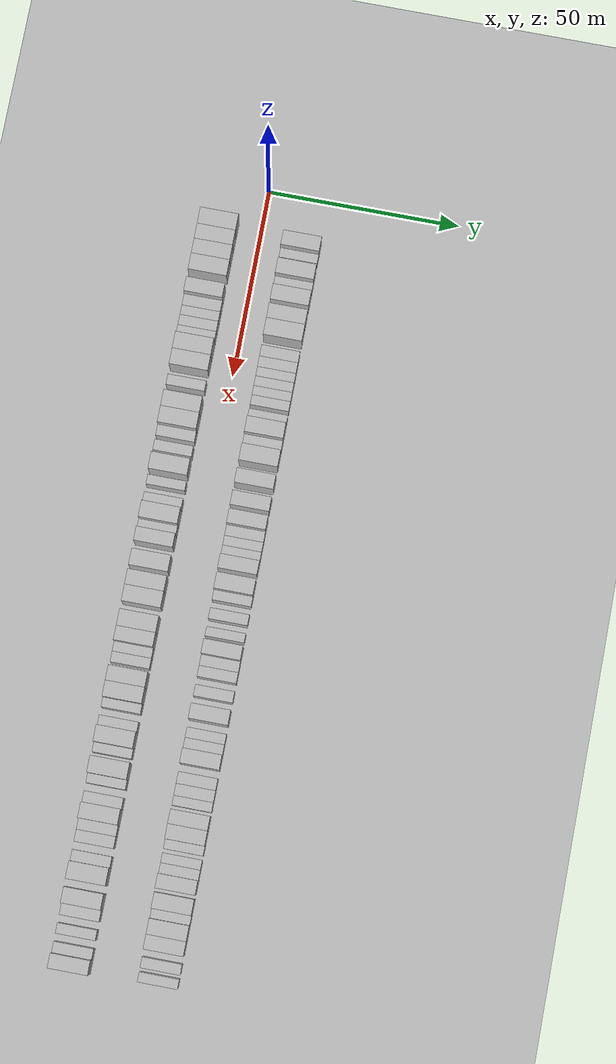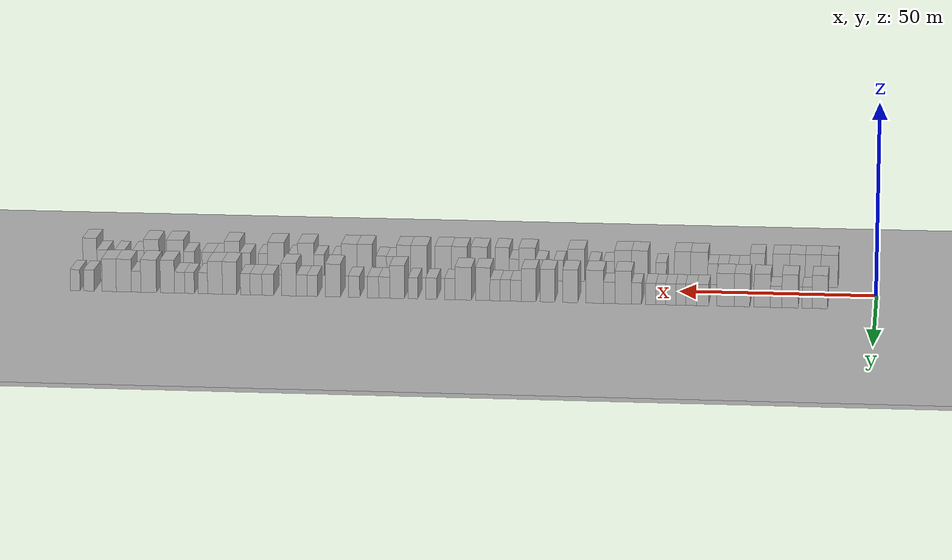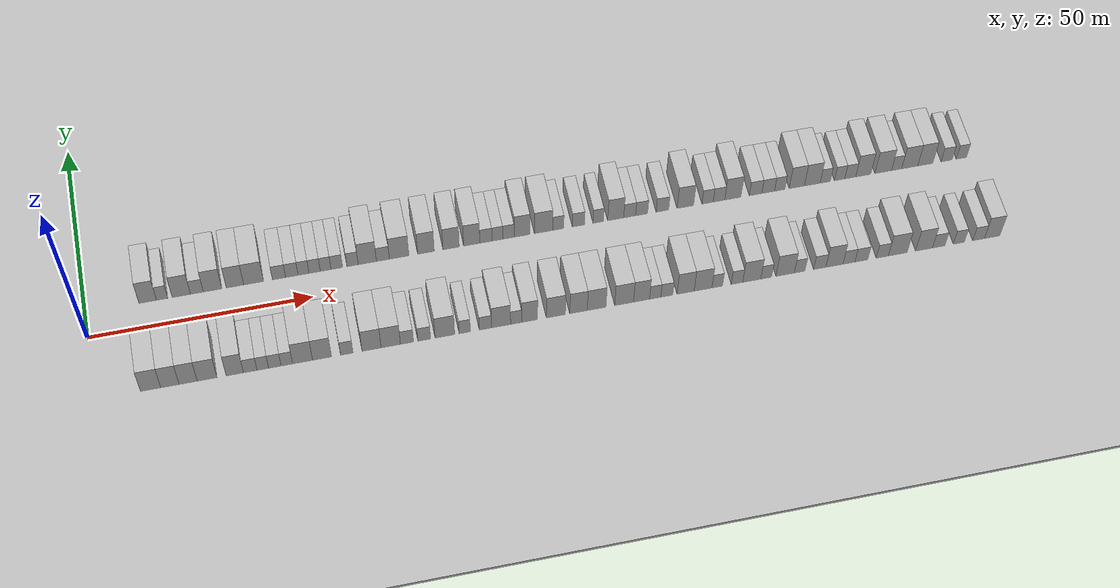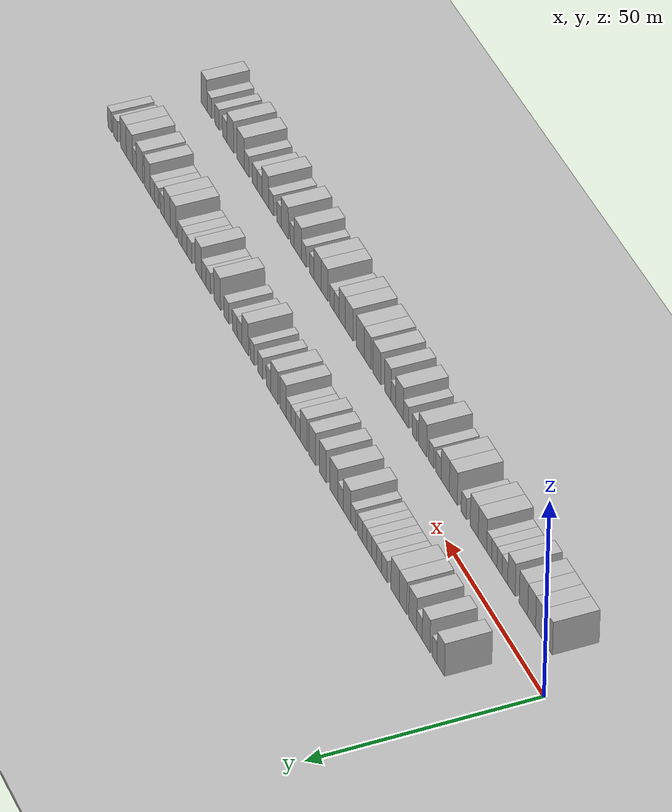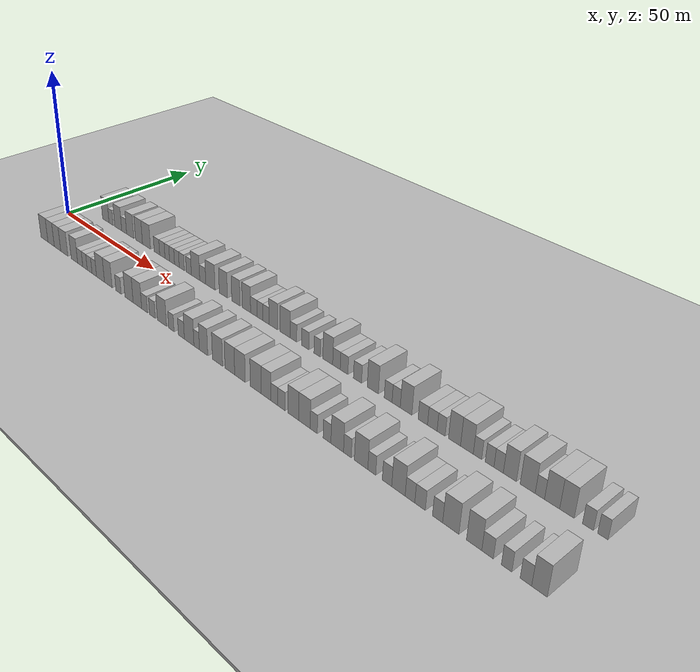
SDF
<?xml version="1.0" encoding="utf-8"?>

<sdf version="1.6">

   <world name="default">

      <gui fullscreen="0">

         <camera name="user_camera">

            <pose>-15 0 4.57585 0 0 0</pose>

            <view_controller>orbit</view_controller>

         </camera>

      </gui>

      <scene>

         <sky>

           <clouds>

             <speed>12</speed>

           </clouds>

         </sky>

         <ambient>0.4 0.4 0.4 1</ambient>

         <background>0.7 0.7 0.7 1</background>

         <shadows>1</shadows>

      </scene>

      <gravity>0 0 -9.8066</gravity>

      <magnetic_field>6e-06 2.3e-05 -4.2e-05</magnetic_field>

      <physics default="0" name="default_physics" type="ode">

         <ode>

            <solver>

               <type>quick</type>

               <iters>10</iters>

               <sor>1.0</sor>

               <use_dynamic_moi_rescaling>0</use_dynamic_moi_rescaling>

            </solver>

            <constraints>

               <cfm>0</cfm>

               <erp>0.2</erp>

               <contact_max_correcting_vel>100</contact_max_correcting_vel>

               <contact_surface_layer>0.001</contact_surface_layer>

            </constraints>

         </ode>

         <max_step_size>0.004</max_step_size>

         <real_time_factor>1</real_time_factor>

         <real_time_update_rate>250</real_time_update_rate>

      </physics>

      <light name="sun" type="directional">

         <cast_shadows>1</cast_shadows>

         <pose>0 0 10 0 0 0</pose>

         <diffuse>0.8 0.8 0.8 1</diffuse>

         <specular>0.2 0.2 0.2 1</specular>

         <attenuation>

            <range>1000</range>

            <constant>0.9</constant>

            <linear>0.01</linear>

            <quadratic>0.001</quadratic>

         </attenuation>

         <direction>-0.5 0.1 -0.9</direction>

      </light>

      <include>

         <name>ground_plane_1</name>

         <uri>model://HANNAS_ground_plane</uri>

         <pose>0 0 0  0 0 0</pose>

      </include>

      <include>

         <name>ground_plane_2</name>

         <uri>model://HANNAS_ground_plane</uri>

         <pose>100 0 0  0 0 0</pose>

      </include>

      <model name="building_1">

         <static>1</static>

         <pose frame="">13.9510 11.0000 0 0.000000 0.000000 1.570796</pose>

         <link name="link">

            <pose frame="">0 0 4.50 0 0 0</pose>

            <collision name="collision">

               <geometry>

                  <box>

                     <size>10.0000 3.9020 9.0000</size>

                  </box>

               </geometry>

               <max_contacts>10</max_contacts>

               <surface>

                  <contact>

                     <ode/>

                  </contact>

                  <bounce/>

                  <friction>

                     <torsional>

                        <ode/>

                     </torsional>

                     <ode/>

                  </friction>

               </surface>

            </collision>

            <visual name="visual">

               <cast_shadows>0</cast_shadows>

               <geometry>

                  <box>

                     <size>10.0000 3.9020 9.0000</size>

                  </box>

               </geometry>

               <material>

                  <script>

                     <uri>model://HANNAS_wall/materials/scripts</uri>

                     <uri>model://HANNAS_wall/materials/textures</uri>

                     <name>vrc/HANNAS_wall</name>

                  </script>

               </material>

            </visual>

            <self_collide>0</self_collide>

            <enable_wind>0</enable_wind>

            <kinematic>0</kinematic>

         </link>

      </model>

      <model name="building_2">

         <static>1</static>

         <pose frame="">17.1490 11.0000 0 0.000000 0.000000 1.570796</pose>

         <link name="link">

            <pose frame="">0 0 3.00 0 0 0</pose>

            <collision name="collision">

               <geometry>

                  <box>

                     <size>10.0000 2.4941 6.0000</size>

                  </box>

               </geometry>

               <max_contacts>10</max_contacts>

               <surface>

                  <contact>

                     <ode/>

                  </contact>

                  <bounce/>

                  <friction>

                     <torsional>

                        <ode/>

                     </torsional>

                     <ode/>

                  </friction>

               </surface>

            </collision>

            <visual name="visual">

               <cast_shadows>0</cast_shadows>

               <geometry>

                  <box>

                     <size>10.0000 2.4941 6.0000</size>

                  </box>

               </geometry>

               <material>

                  <script>

                     <uri>model://HANNAS_wall/materials/scripts</uri>

                     <uri>model://HANNAS_wall/materials/textures</uri>

                     <name>vrc/HANNAS_wall</name>

                  </script>

               </material>

            </visual>

            <self_collide>0</self_collide>

            <enable_wind>0</enable_wind>

            <kinematic>0</kinematic>

         </link>

      </model>

      <model name="building_3">

         <static>1</static>

         <pose frame="">21.4325 11.0000 0 0.000000 0.000000 1.570796</pose>

         <link name="link">

            <pose frame="">0 0 4.50 0 0 0</pose>

            <collision name="collision">

               <geometry>

                  <box>

                     <size>10.0000 4.0729 9.0000</size>

                  </box>

               </geometry>

               <max_contacts>10</max_contacts>

               <surface>

                  <contact>

                     <ode/>

                  </contact>

                  <bounce/>

                  <friction>

                     <torsional>

                        <ode/>

                     </torsional>

                     <ode/>

                  </friction>

               </surface>

            </collision>

            <visual name="visual">

               <cast_shadows>0</cast_shadows>

               <geometry>

                  <box>

                     <size>10.0000 4.0729 9.0000</size>

                  </box>

               </geometry>

               <material>

                  <script>

                     <uri>model://HANNAS_wall/materials/scripts</uri>

                     <uri>model://HANNAS_wall/materials/textures</uri>

                     <name>vrc/HANNAS_wall</name>

                  </script>

               </material>

            </visual>

            <self_collide>0</self_collide>

            <enable_wind>0</enable_wind>

            <kinematic>0</kinematic>

         </link>

      </model>

      <model name="building_4">

         <static>1</static>

         <pose frame="">24.9111 11.0000 0 0.000000 0.000000 1.570796</pose>

         <link name="link">

            <pose frame="">0 0 3.00 0 0 0</pose>

            <collision name="collision">

               <geometry>

                  <box>

                     <size>10.0000 2.8844 6.0000</size>

                  </box>

               </geometry>

               <max_contacts>10</max_contacts>

               <surface>

                  <contact>

                     <ode/>

                  </contact>

                  <bounce/>

                  <friction>

                     <torsional>

                        <ode/>

                     </torsional>

                     <ode/>

                  </friction>

               </surface>

            </collision>

            <visual name="visual">

               <cast_shadows>0</cast_shadows>

               <geometry>

                  <box>

                     <size>10.0000 2.8844 6.0000</size>

                  </box>

               </geometry>

               <material>

                  <script>

                     <uri>model://HANNAS_wall/materials/scripts</uri>

                     <uri>model://HANNAS_wall/materials/textures</uri>

                     <name>vrc/HANNAS_wall</name>

                  </script>

               </material>

            </visual>

            <self_collide>0</self_collide>

            <enable_wind>0</enable_wind>

            <kinematic>0</kinematic>

         </link>

      </model>

      <model name="building_5">

         <static>1</static>

         <pose frame="">28.4173 11.0000 0 0.000000 0.000000 1.570796</pose>

         <link name="link">

            <pose frame="">0 0 4.50 0 0 0</pose>

            <collision name="collision">

               <geometry>

                  <box>

                     <size>10.0000 4.1281 9.0000</size>

                  </box>

               </geometry>

               <max_contacts>10</max_contacts>

               <surface>

                  <contact>

                     <ode/>

                  </contact>

                  <bounce/>

                  <friction>

                     <torsional>

                        <ode/>

                     </torsional>

                     <ode/>

                  </friction>

               </surface>

            </collision>

            <visual name="visual">

               <cast_shadows>0</cast_shadows>

               <geometry>

                  <box>

                     <size>10.0000 4.1281 9.0000</size>

                  </box>

               </geometry>

               <material>

                  <script>

                     <uri>model://HANNAS_wall/materials/scripts</uri>

                     <uri>model://HANNAS_wall/materials/textures</uri>

                     <name>vrc/HANNAS_wall</name>

                  </script>

               </material>

            </visual>

            <self_collide>0</self_collide>

            <enable_wind>0</enable_wind>

            <kinematic>0</kinematic>

         </link>

      </model>

      <model name="building_6">

         <static>1</static>

         <pose frame="">33.4345 11.0000 0 0.000000 0.000000 1.570796</pose>

         <link name="link">

            <pose frame="">0 0 4.50 0 0 0</pose>

            <collision name="collision">

               <geometry>

                  <box>

                     <size>10.0000 3.9062 9.0000</size>

                  </box>

               </geometry>

               <max_contacts>10</max_contacts>

               <surface>

                  <contact>

                     <ode/>

                  </contact>

                  <bounce/>

                  <friction>

                     <torsional>

                        <ode/>

                     </torsional>

                     <ode/>

                  </friction>

               </surface>

            </collision>

            <visual name="visual">

               <cast_shadows>0</cast_shadows>

               <geometry>

                  <box>

                     <size>10.0000 3.9062 9.0000</size>

                  </box>

               </geometry>

               <material>

                  <script>

                     <uri>model://HANNAS_wall/materials/scripts</uri>

                     <uri>model://HANNAS_wall/materials/textures</uri>

                     <name>vrc/HANNAS_wall</name>

                  </script>

               </material>

            </visual>

            <self_collide>0</self_collide>

            <enable_wind>0</enable_wind>

            <kinematic>0</kinematic>

         </link>

      </model>

      <model name="building_7">

         <static>1</static>

         <pose frame="">37.6217 11.0000 0 0.000000 0.000000 1.570796</pose>

         <link name="link">

            <pose frame="">0 0 4.50 0 0 0</pose>

            <collision name="collision">

               <geometry>

                  <box>

                     <size>10.0000 4.4682 9.0000</size>

                  </box>

               </geometry>

               <max_contacts>10</max_contacts>

               <surface>

                  <contact>

                     <ode/>

                  </contact>

                  <bounce/>

                  <friction>

                     <torsional>

                        <ode/>

                     </torsional>

                     <ode/>

                  </friction>

               </surface>

            </collision>

            <visual name="visual">

               <cast_shadows>0</cast_shadows>

               <geometry>

                  <box>

                     <size>10.0000 4.4682 9.0000</size>

                  </box>

               </geometry>

               <material>

                  <script>

                     <uri>model://HANNAS_wall/materials/scripts</uri>

                     <uri>model://HANNAS_wall/materials/textures</uri>

                     <name>vrc/HANNAS_wall</name>

                  </script>

               </material>

            </visual>

            <self_collide>0</self_collide>

            <enable_wind>0</enable_wind>

            <kinematic>0</kinematic>

         </link>

      </model>

      <model name="building_8">

         <static>1</static>

         <pose frame="">43.3466 11.0000 0 0.000000 0.000000 1.570796</pose>

         <link name="link">

            <pose frame="">0 0 3.00 0 0 0</pose>

            <collision name="collision">

               <geometry>

                  <box>

                     <size>10.0000 2.9816 6.0000</size>

                  </box>

               </geometry>

               <max_contacts>10</max_contacts>

               <surface>

                  <contact>

                     <ode/>

                  </contact>

                  <bounce/>

                  <friction>

                     <torsional>

                        <ode/>

                     </torsional>

                     <ode/>

                  </friction>

               </surface>

            </collision>

            <visual name="visual">

               <cast_shadows>0</cast_shadows>

               <geometry>

                  <box>

                     <size>10.0000 2.9816 6.0000</size>

                  </box>

               </geometry>

               <material>

                  <script>

                     <uri>model://HANNAS_wall/materials/scripts</uri>

                     <uri>model://HANNAS_wall/materials/textures</uri>

                     <name>vrc/HANNAS_wall</name>

                  </script>

               </material>

            </visual>

            <self_collide>0</self_collide>

            <enable_wind>0</enable_wind>

            <kinematic>0</kinematic>

         </link>

      </model>

      <model name="building_9">

         <static>1</static>

         <pose frame="">46.2434 11.0000 0 0.000000 0.000000 1.570796</pose>

         <link name="link">

            <pose frame="">0 0 3.00 0 0 0</pose>

            <collision name="collision">

               <geometry>

                  <box>

                     <size>10.0000 2.8121 6.0000</size>

                  </box>

               </geometry>

               <max_contacts>10</max_contacts>

               <surface>

                  <contact>

                     <ode/>

                  </contact>

                  <bounce/>

                  <friction>

                     <torsional>

                        <ode/>

                     </torsional>

                     <ode/>

                  </friction>

               </surface>

            </collision>

            <visual name="visual">

               <cast_shadows>0</cast_shadows>

               <geometry>

                  <box>

                     <size>10.0000 2.8121 6.0000</size>

                  </box>

               </geometry>

               <material>

                  <script>

                     <uri>model://HANNAS_wall/materials/scripts</uri>

                     <uri>model://HANNAS_wall/materials/textures</uri>

                     <name>vrc/HANNAS_wall</name>

                  </script>

               </material>

            </visual>

            <self_collide>0</self_collide>

            <enable_wind>0</enable_wind>

            <kinematic>0</kinematic>

         </link>

      </model>

      <model name="building_10">

         <static>1</static>

         <pose frame="">48.8798 11.0000 0 0.000000 0.000000 1.570796</pose>

         <link name="link">

            <pose frame="">0 0 3.00 0 0 0</pose>

            <collision name="collision">

               <geometry>

                  <box>

                     <size>10.0000 2.4606 6.0000</size>

                  </box>

               </geometry>

               <max_contacts>10</max_contacts>

               <surface>

                  <contact>

                     <ode/>

                  </contact>

                  <bounce/>

                  <friction>

                     <torsional>

                        <ode/>

                     </torsional>

                     <ode/>

                  </friction>

               </surface>

            </collision>

            <visual name="visual">

               <cast_shadows>0</cast_shadows>

               <geometry>

                  <box>

                     <size>10.0000 2.4606 6.0000</size>

                  </box>

               </geometry>

               <material>

                  <script>

                     <uri>model://HANNAS_wall/materials/scripts</uri>

                     <uri>model://HANNAS_wall/materials/textures</uri>

                     <name>vrc/HANNAS_wall</name>

                  </script>

               </material>

            </visual>

            <self_collide>0</self_collide>

            <enable_wind>0</enable_wind>

            <kinematic>0</kinematic>

         </link>

      </model>

      <model name="building_11">

         <static>1</static>

         <pose frame="">51.3890 11.0000 0 0.000000 0.000000 1.570796</pose>

         <link name="link">

            <pose frame="">0 0 3.00 0 0 0</pose>

            <collision name="collision">

               <geometry>

                  <box>

                     <size>10.0000 2.5578 6.0000</size>

                  </box>

               </geometry>

               <max_contacts>10</max_contacts>

               <surface>

                  <contact>

                     <ode/>

                  </contact>

                  <bounce/>

                  <friction>

                     <torsional>

                        <ode/>

                     </torsional>

                     <ode/>

                  </friction>

               </surface>

            </collision>

            <visual name="visual">

               <cast_shadows>0</cast_shadows>

               <geometry>

                  <box>

                     <size>10.0000 2.5578 6.0000</size>

                  </box>

               </geometry>

               <material>

                  <script>

                     <uri>model://HANNAS_wall/materials/scripts</uri>

                     <uri>model://HANNAS_wall/materials/textures</uri>

                     <name>vrc/HANNAS_wall</name>

                  </script>

               </material>

            </visual>

            <self_collide>0</self_collide>

            <enable_wind>0</enable_wind>

            <kinematic>0</kinematic>

         </link>

      </model>

      <model name="building_12">

         <static>1</static>

         <pose frame="">53.8851 11.0000 0 0.000000 0.000000 1.570796</pose>

         <link name="link">

            <pose frame="">0 0 3.00 0 0 0</pose>

            <collision name="collision">

               <geometry>

                  <box>

                     <size>10.0000 2.4345 6.0000</size>

                  </box>

               </geometry>

               <max_contacts>10</max_contacts>

               <surface>

                  <contact>

                     <ode/>

                  </contact>

                  <bounce/>

                  <friction>

                     <torsional>

                        <ode/>

                     </torsional>

                     <ode/>

                  </friction>

               </surface>

            </collision>

            <visual name="visual">

               <cast_shadows>0</cast_shadows>

               <geometry>

                  <box>

                     <size>10.0000 2.4345 6.0000</size>

                  </box>

               </geometry>

               <material>

                  <script>

                     <uri>model://HANNAS_wall/materials/scripts</uri>

                     <uri>model://HANNAS_wall/materials/textures</uri>

                     <name>vrc/HANNAS_wall</name>

                  </script>

               </material>

            </visual>

            <self_collide>0</self_collide>

            <enable_wind>0</enable_wind>

            <kinematic>0</kinematic>

         </link>

      </model>

      <model name="building_13">

         <static>1</static>

         <pose frame="">56.4099 11.0000 0 0.000000 0.000000 1.570796</pose>

         <link name="link">

            <pose frame="">0 0 3.00 0 0 0</pose>

            <collision name="collision">

               <geometry>

                  <box>

                     <size>10.0000 2.6151 6.0000</size>

                  </box>

               </geometry>

               <max_contacts>10</max_contacts>

               <surface>

                  <contact>

                     <ode/>

                  </contact>

                  <bounce/>

                  <friction>

                     <torsional>

                        <ode/>

                     </torsional>

                     <ode/>

                  </friction>

               </surface>

            </collision>

            <visual name="visual">

               <cast_shadows>0</cast_shadows>

               <geometry>

                  <box>

                     <size>10.0000 2.6151 6.0000</size>

                  </box>

               </geometry>

               <material>

                  <script>

                     <uri>model://HANNAS_wall/materials/scripts</uri>

                     <uri>model://HANNAS_wall/materials/textures</uri>

                     <name>vrc/HANNAS_wall</name>

                  </script>

               </material>

            </visual>

            <self_collide>0</self_collide>

            <enable_wind>0</enable_wind>

            <kinematic>0</kinematic>

         </link>

      </model>

      <model name="building_14">

         <static>1</static>

         <pose frame="">59.9889 11.0000 0 0.000000 0.000000 1.570796</pose>

         <link name="link">

            <pose frame="">0 0 3.00 0 0 0</pose>

            <collision name="collision">

               <geometry>

                  <box>

                     <size>10.0000 2.5429 6.0000</size>

                  </box>

               </geometry>

               <max_contacts>10</max_contacts>

               <surface>

                  <contact>

                     <ode/>

                  </contact>

                  <bounce/>

                  <friction>

                     <torsional>

                        <ode/>

                     </torsional>

                     <ode/>

                  </friction>

               </surface>

            </collision>

            <visual name="visual">

               <cast_shadows>0</cast_shadows>

               <geometry>

                  <box>

                     <size>10.0000 2.5429 6.0000</size>

                  </box>

               </geometry>

               <material>

                  <script>

                     <uri>model://HANNAS_wall/materials/scripts</uri>

                     <uri>model://HANNAS_wall/materials/textures</uri>

                     <name>vrc/HANNAS_wall</name>

                  </script>

               </material>

            </visual>

            <self_collide>0</self_collide>

            <enable_wind>0</enable_wind>

            <kinematic>0</kinematic>

         </link>

      </model>

      <model name="building_15">

         <static>1</static>

         <pose frame="">63.3386 11.0000 0 0.000000 0.000000 1.570796</pose>

         <link name="link">

            <pose frame="">0 0 4.50 0 0 0</pose>

            <collision name="collision">

               <geometry>

                  <box>

                     <size>10.0000 4.1566 9.0000</size>

                  </box>

               </geometry>

               <max_contacts>10</max_contacts>

               <surface>

                  <contact>

                     <ode/>

                  </contact>

                  <bounce/>

                  <friction>

                     <torsional>

                        <ode/>

                     </torsional>

                     <ode/>

                  </friction>

               </surface>

            </collision>

            <visual name="visual">

               <cast_shadows>0</cast_shadows>

               <geometry>

                  <box>

                     <size>10.0000 4.1566 9.0000</size>

                  </box>

               </geometry>

               <material>

                  <script>

                     <uri>model://HANNAS_wall/materials/scripts</uri>

                     <uri>model://HANNAS_wall/materials/textures</uri>

                     <name>vrc/HANNAS_wall</name>

                  </script>

               </material>

            </visual>

            <self_collide>0</self_collide>

            <enable_wind>0</enable_wind>

            <kinematic>0</kinematic>

         </link>

      </model>

      <model name="building_16">

         <static>1</static>

         <pose frame="">66.8907 11.0000 0 0.000000 0.000000 1.570796</pose>

         <link name="link">

            <pose frame="">0 0 3.00 0 0 0</pose>

            <collision name="collision">

               <geometry>

                  <box>

                     <size>10.0000 2.9475 6.0000</size>

                  </box>

               </geometry>

               <max_contacts>10</max_contacts>

               <surface>

                  <contact>

                     <ode/>

                  </contact>

                  <bounce/>

                  <friction>

                     <torsional>

                        <ode/>

                     </torsional>

                     <ode/>

                  </friction>

               </surface>

            </collision>

            <visual name="visual">

               <cast_shadows>0</cast_shadows>

               <geometry>

                  <box>

                     <size>10.0000 2.9475 6.0000</size>

                  </box>

               </geometry>

               <material>

                  <script>

                     <uri>model://HANNAS_wall/materials/scripts</uri>

                     <uri>model://HANNAS_wall/materials/textures</uri>

                     <name>vrc/HANNAS_wall</name>

                  </script>

               </material>

            </visual>

            <self_collide>0</self_collide>

            <enable_wind>0</enable_wind>

            <kinematic>0</kinematic>

         </link>

      </model>

      <model name="building_17">

         <static>1</static>

         <pose frame="">70.5925 11.0000 0 0.000000 0.000000 1.570796</pose>

         <link name="link">

            <pose frame="">0 0 4.50 0 0 0</pose>

            <collision name="collision">

               <geometry>

                  <box>

                     <size>10.0000 4.4562 9.0000</size>

                  </box>

               </geometry>

               <max_contacts>10</max_contacts>

               <surface>

                  <contact>

                     <ode/>

                  </contact>

                  <bounce/>

                  <friction>

                     <torsional>

                        <ode/>

                     </torsional>

                     <ode/>

                  </friction>

               </surface>

            </collision>

            <visual name="visual">

               <cast_shadows>0</cast_shadows>

               <geometry>

                  <box>

                     <size>10.0000 4.4562 9.0000</size>

                  </box>

               </geometry>

               <material>

                  <script>

                     <uri>model://HANNAS_wall/materials/scripts</uri>

                     <uri>model://HANNAS_wall/materials/textures</uri>

                     <name>vrc/HANNAS_wall</name>

                  </script>

               </material>

            </visual>

            <self_collide>0</self_collide>

            <enable_wind>0</enable_wind>

            <kinematic>0</kinematic>

         </link>

      </model>

      <model name="building_18">

         <static>1</static>

         <pose frame="">76.7253 11.0000 0 0.000000 0.000000 1.570796</pose>

         <link name="link">

            <pose frame="">0 0 4.50 0 0 0</pose>

            <collision name="collision">

               <geometry>

                  <box>

                     <size>10.0000 3.8095 9.0000</size>

                  </box>

               </geometry>

               <max_contacts>10</max_contacts>

               <surface>

                  <contact>

                     <ode/>

                  </contact>

                  <bounce/>

                  <friction>

                     <torsional>

                        <ode/>

                     </torsional>

                     <ode/>

                  </friction>

               </surface>

            </collision>

            <visual name="visual">

               <cast_shadows>0</cast_shadows>

               <geometry>

                  <box>

                     <size>10.0000 3.8095 9.0000</size>

                  </box>

               </geometry>

               <material>

                  <script>

                     <uri>model://HANNAS_wall/materials/scripts</uri>

                     <uri>model://HANNAS_wall/materials/textures</uri>

                     <name>vrc/HANNAS_wall</name>

                  </script>

               </material>

            </visual>

            <self_collide>0</self_collide>

            <enable_wind>0</enable_wind>

            <kinematic>0</kinematic>

         </link>

      </model>

      <model name="building_19">

         <static>1</static>

         <pose frame="">82.5011 11.0000 0 0.000000 0.000000 1.570796</pose>

         <link name="link">

            <pose frame="">0 0 4.50 0 0 0</pose>

            <collision name="collision">

               <geometry>

                  <box>

                     <size>10.0000 3.7421 9.0000</size>

                  </box>

               </geometry>

               <max_contacts>10</max_contacts>

               <surface>

                  <contact>

                     <ode/>

                  </contact>

                  <bounce/>

                  <friction>

                     <torsional>

                        <ode/>

                     </torsional>

                     <ode/>

                  </friction>

               </surface>

            </collision>

            <visual name="visual">

               <cast_shadows>0</cast_shadows>

               <geometry>

                  <box>

                     <size>10.0000 3.7421 9.0000</size>

                  </box>

               </geometry>

               <material>

                  <script>

                     <uri>model://HANNAS_wall/materials/scripts</uri>

                     <uri>model://HANNAS_wall/materials/textures</uri>

                     <name>vrc/HANNAS_wall</name>

                  </script>

               </material>

            </visual>

            <self_collide>0</self_collide>

            <enable_wind>0</enable_wind>

            <kinematic>0</kinematic>

         </link>

      </model>

      <model name="building_20">

         <static>1</static>

         <pose frame="">87.2350 11.0000 0 0.000000 0.000000 1.570796</pose>

         <link name="link">

            <pose frame="">0 0 4.50 0 0 0</pose>

            <collision name="collision">

               <geometry>

                  <box>

                     <size>10.0000 3.7256 9.0000</size>

                  </box>

               </geometry>

               <max_contacts>10</max_contacts>

               <surface>

                  <contact>

                     <ode/>

                  </contact>

                  <bounce/>

                  <friction>

                     <torsional>

                        <ode/>

                     </torsional>

                     <ode/>

                  </friction>

               </surface>

            </collision>

            <visual name="visual">

               <cast_shadows>0</cast_shadows>

               <geometry>

                  <box>

                     <size>10.0000 3.7256 9.0000</size>

                  </box>

               </geometry>

               <material>

                  <script>

                     <uri>model://HANNAS_wall/materials/scripts</uri>

                     <uri>model://HANNAS_wall/materials/textures</uri>

                     <name>vrc/HANNAS_wall</name>

                  </script>

               </material>

            </visual>

            <self_collide>0</self_collide>

            <enable_wind>0</enable_wind>

            <kinematic>0</kinematic>

         </link>

      </model>

      <model name="building_21">

         <static>1</static>

         <pose frame="">90.4984 11.0000 0 0.000000 0.000000 1.570796</pose>

         <link name="link">

            <pose frame="">0 0 3.00 0 0 0</pose>

            <collision name="collision">

               <geometry>

                  <box>

                     <size>10.0000 2.8013 6.0000</size>

                  </box>

               </geometry>

               <max_contacts>10</max_contacts>

               <surface>

                  <contact>

                     <ode/>

                  </contact>

                  <bounce/>

                  <friction>

                     <torsional>

                        <ode/>

                     </torsional>

                     <ode/>

                  </friction>

               </surface>

            </collision>

            <visual name="visual">

               <cast_shadows>0</cast_shadows>

               <geometry>

                  <box>

                     <size>10.0000 2.8013 6.0000</size>

                  </box>

               </geometry>

               <material>

                  <script>

                     <uri>model://HANNAS_wall/materials/scripts</uri>

                     <uri>model://HANNAS_wall/materials/textures</uri>

                     <name>vrc/HANNAS_wall</name>

                  </script>

               </material>

            </visual>

            <self_collide>0</self_collide>

            <enable_wind>0</enable_wind>

            <kinematic>0</kinematic>

         </link>

      </model>

      <model name="building_22">

         <static>1</static>

         <pose frame="">93.1479 11.0000 0 0.000000 0.000000 1.570796</pose>

         <link name="link">

            <pose frame="">0 0 3.00 0 0 0</pose>

            <collision name="collision">

               <geometry>

                  <box>

                     <size>10.0000 2.4976 6.0000</size>

                  </box>

               </geometry>

               <max_contacts>10</max_contacts>

               <surface>

                  <contact>

                     <ode/>

                  </contact>

                  <bounce/>

                  <friction>

                     <torsional>

                        <ode/>

                     </torsional>

                     <ode/>

                  </friction>

               </surface>

            </collision>

            <visual name="visual">

               <cast_shadows>0</cast_shadows>

               <geometry>

                  <box>

                     <size>10.0000 2.4976 6.0000</size>

                  </box>

               </geometry>

               <material>

                  <script>

                     <uri>model://HANNAS_wall/materials/scripts</uri>

                     <uri>model://HANNAS_wall/materials/textures</uri>

                     <name>vrc/HANNAS_wall</name>

                  </script>

               </material>

            </visual>

            <self_collide>0</self_collide>

            <enable_wind>0</enable_wind>

            <kinematic>0</kinematic>

         </link>

      </model>

      <model name="building_23">

         <static>1</static>

         <pose frame="">95.7047 11.0000 0 0.000000 0.000000 1.570796</pose>

         <link name="link">

            <pose frame="">0 0 3.00 0 0 0</pose>

            <collision name="collision">

               <geometry>

                  <box>

                     <size>10.0000 2.6161 6.0000</size>

                  </box>

               </geometry>

               <max_contacts>10</max_contacts>

               <surface>

                  <contact>

                     <ode/>

                  </contact>

                  <bounce/>

                  <friction>

                     <torsional>

                        <ode/>

                     </torsional>

                     <ode/>

                  </friction>

               </surface>

            </collision>

            <visual name="visual">

               <cast_shadows>0</cast_shadows>

               <geometry>

                  <box>

                     <size>10.0000 2.6161 6.0000</size>

                  </box>

               </geometry>

               <material>

                  <script>

                     <uri>model://HANNAS_wall/materials/scripts</uri>

                     <uri>model://HANNAS_wall/materials/textures</uri>

                     <name>vrc/HANNAS_wall</name>

                  </script>

               </material>

            </visual>

            <self_collide>0</self_collide>

            <enable_wind>0</enable_wind>

            <kinematic>0</kinematic>

         </link>

      </model>

      <model name="building_24">

         <static>1</static>

         <pose frame="">98.8529 11.0000 0 0.000000 0.000000 1.570796</pose>

         <link name="link">

            <pose frame="">0 0 4.50 0 0 0</pose>

            <collision name="collision">

               <geometry>

                  <box>

                     <size>10.0000 3.6804 9.0000</size>

                  </box>

               </geometry>

               <max_contacts>10</max_contacts>

               <surface>

                  <contact>

                     <ode/>

                  </contact>

                  <bounce/>

                  <friction>

                     <torsional>

                        <ode/>

                     </torsional>

                     <ode/>

                  </friction>

               </surface>

            </collision>

            <visual name="visual">

               <cast_shadows>0</cast_shadows>

               <geometry>

                  <box>

                     <size>10.0000 3.6804 9.0000</size>

                  </box>

               </geometry>

               <material>

                  <script>

                     <uri>model://HANNAS_wall/materials/scripts</uri>

                     <uri>model://HANNAS_wall/materials/textures</uri>

                     <name>vrc/HANNAS_wall</name>

                  </script>

               </material>

            </visual>

            <self_collide>0</self_collide>

            <enable_wind>0</enable_wind>

            <kinematic>0</kinematic>

         </link>

      </model>

      <model name="building_25">

         <static>1</static>

         <pose frame="">103.8006 11.0000 0 0.000000 0.000000 1.570796</pose>

         <link name="link">

            <pose frame="">0 0 4.50 0 0 0</pose>

            <collision name="collision">

               <geometry>

                  <box>

                     <size>10.0000 4.2151 9.0000</size>

                  </box>

               </geometry>

               <max_contacts>10</max_contacts>

               <surface>

                  <contact>

                     <ode/>

                  </contact>

                  <bounce/>

                  <friction>

                     <torsional>

                        <ode/>

                     </torsional>

                     <ode/>

                  </friction>

               </surface>

            </collision>

            <visual name="visual">

               <cast_shadows>0</cast_shadows>

               <geometry>

                  <box>

                     <size>10.0000 4.2151 9.0000</size>

                  </box>

               </geometry>

               <material>

                  <script>

                     <uri>model://HANNAS_wall/materials/scripts</uri>

                     <uri>model://HANNAS_wall/materials/textures</uri>

                     <name>vrc/HANNAS_wall</name>

                  </script>

               </material>

            </visual>

            <self_collide>0</self_collide>

            <enable_wind>0</enable_wind>

            <kinematic>0</kinematic>

         </link>

      </model>

      <model name="building_26">

         <static>1</static>

         <pose frame="">107.2068 11.0000 0 0.000000 0.000000 1.570796</pose>

         <link name="link">

            <pose frame="">0 0 3.00 0 0 0</pose>

            <collision name="collision">

               <geometry>

                  <box>

                     <size>10.0000 2.5972 6.0000</size>

                  </box>

               </geometry>

               <max_contacts>10</max_contacts>

               <surface>

                  <contact>

                     <ode/>

                  </contact>

                  <bounce/>

                  <friction>

                     <torsional>

                        <ode/>

                     </torsional>

                     <ode/>

                  </friction>

               </surface>

            </collision>

            <visual name="visual">

               <cast_shadows>0</cast_shadows>

               <geometry>

                  <box>

                     <size>10.0000 2.5972 6.0000</size>

                  </box>

               </geometry>

               <material>

                  <script>

                     <uri>model://HANNAS_wall/materials/scripts</uri>

                     <uri>model://HANNAS_wall/materials/textures</uri>

                     <name>vrc/HANNAS_wall</name>

                  </script>

               </material>

            </visual>

            <self_collide>0</self_collide>

            <enable_wind>0</enable_wind>

            <kinematic>0</kinematic>

         </link>

      </model>

      <model name="building_27">

         <static>1</static>

         <pose frame="">111.9166 11.0000 0 0.000000 0.000000 1.570796</pose>

         <link name="link">

            <pose frame="">0 0 3.00 0 0 0</pose>

            <collision name="collision">

               <geometry>

                  <box>

                     <size>10.0000 2.8224 6.0000</size>

                  </box>

               </geometry>

               <max_contacts>10</max_contacts>

               <surface>

                  <contact>

                     <ode/>

                  </contact>

                  <bounce/>

                  <friction>

                     <torsional>

                        <ode/>

                     </torsional>

                     <ode/>

                  </friction>

               </surface>

            </collision>

            <visual name="visual">

               <cast_shadows>0</cast_shadows>

               <geometry>

                  <box>

                     <size>10.0000 2.8224 6.0000</size>

                  </box>

               </geometry>

               <material>

                  <script>

                     <uri>model://HANNAS_wall/materials/scripts</uri>

                     <uri>model://HANNAS_wall/materials/textures</uri>

                     <name>vrc/HANNAS_wall</name>

                  </script>

               </material>

            </visual>

            <self_collide>0</self_collide>

            <enable_wind>0</enable_wind>

            <kinematic>0</kinematic>

         </link>

      </model>

      <model name="building_28">

         <static>1</static>

         <pose frame="">116.5382 11.0000 0 0.000000 0.000000 1.570796</pose>

         <link name="link">

            <pose frame="">0 0 3.00 0 0 0</pose>

            <collision name="collision">

               <geometry>

                  <box>

                     <size>10.0000 2.4210 6.0000</size>

                  </box>

               </geometry>

               <max_contacts>10</max_contacts>

               <surface>

                  <contact>

                     <ode/>

                  </contact>

                  <bounce/>

                  <friction>

                     <torsional>

                        <ode/>

                     </torsional>

                     <ode/>

                  </friction>

               </surface>

            </collision>

            <visual name="visual">

               <cast_shadows>0</cast_shadows>

               <geometry>

                  <box>

                     <size>10.0000 2.4210 6.0000</size>

                  </box>

               </geometry>

               <material>

                  <script>

                     <uri>model://HANNAS_wall/materials/scripts</uri>

                     <uri>model://HANNAS_wall/materials/textures</uri>

                     <name>vrc/HANNAS_wall</name>

                  </script>

               </material>

            </visual>

            <self_collide>0</self_collide>

            <enable_wind>0</enable_wind>

            <kinematic>0</kinematic>

         </link>

      </model>

      <model name="building_29">

         <static>1</static>

         <pose frame="">120.6174 11.0000 0 0.000000 0.000000 1.570796</pose>

         <link name="link">

            <pose frame="">0 0 4.50 0 0 0</pose>

            <collision name="collision">

               <geometry>

                  <box>

                     <size>10.0000 3.7374 9.0000</size>

                  </box>

               </geometry>

               <max_contacts>10</max_contacts>

               <surface>

                  <contact>

                     <ode/>

                  </contact>

                  <bounce/>

                  <friction>

                     <torsional>

                        <ode/>

                     </torsional>

                     <ode/>

                  </friction>

               </surface>

            </collision>

            <visual name="visual">

               <cast_shadows>0</cast_shadows>

               <geometry>

                  <box>

                     <size>10.0000 3.7374 9.0000</size>

                  </box>

               </geometry>

               <material>

                  <script>

                     <uri>model://HANNAS_wall/materials/scripts</uri>

                     <uri>model://HANNAS_wall/materials/textures</uri>

                     <name>vrc/HANNAS_wall</name>

                  </script>

               </material>

            </visual>

            <self_collide>0</self_collide>

            <enable_wind>0</enable_wind>

            <kinematic>0</kinematic>

         </link>

      </model>

      <model name="building_30">

         <static>1</static>

         <pose frame="">123.8850 11.0000 0 0.000000 0.000000 1.570796</pose>

         <link name="link">

            <pose frame="">0 0 3.00 0 0 0</pose>

            <collision name="collision">

               <geometry>

                  <box>

                     <size>10.0000 2.7978 6.0000</size>

                  </box>

               </geometry>

               <max_contacts>10</max_contacts>

               <surface>

                  <contact>

                     <ode/>

                  </contact>

                  <bounce/>

                  <friction>

                     <torsional>

                        <ode/>

                     </torsional>

                     <ode/>

                  </friction>

               </surface>

            </collision>

            <visual name="visual">

               <cast_shadows>0</cast_shadows>

               <geometry>

                  <box>

                     <size>10.0000 2.7978 6.0000</size>

                  </box>

               </geometry>

               <material>

                  <script>

                     <uri>model://HANNAS_wall/materials/scripts</uri>

                     <uri>model://HANNAS_wall/materials/textures</uri>

                     <name>vrc/HANNAS_wall</name>

                  </script>

               </material>

            </visual>

            <self_collide>0</self_collide>

            <enable_wind>0</enable_wind>

            <kinematic>0</kinematic>

         </link>

      </model>

      <model name="building_31">

         <static>1</static>

         <pose frame="">126.6897 11.0000 0 0.000000 0.000000 1.570796</pose>

         <link name="link">

            <pose frame="">0 0 3.00 0 0 0</pose>

            <collision name="collision">

               <geometry>

                  <box>

                     <size>10.0000 2.8115 6.0000</size>

                  </box>

               </geometry>

               <max_contacts>10</max_contacts>

               <surface>

                  <contact>

                     <ode/>

                  </contact>

                  <bounce/>

                  <friction>

                     <torsional>

                        <ode/>

                     </torsional>

                     <ode/>

                  </friction>

               </surface>

            </collision>

            <visual name="visual">

               <cast_shadows>0</cast_shadows>

               <geometry>

                  <box>

                     <size>10.0000 2.8115 6.0000</size>

                  </box>

               </geometry>

               <material>

                  <script>

                     <uri>model://HANNAS_wall/materials/scripts</uri>

                     <uri>model://HANNAS_wall/materials/textures</uri>

                     <name>vrc/HANNAS_wall</name>

                  </script>

               </material>

            </visual>

            <self_collide>0</self_collide>

            <enable_wind>0</enable_wind>

            <kinematic>0</kinematic>

         </link>

      </model>

      <model name="building_32">

         <static>1</static>

         <pose frame="">131.5565 11.0000 0 0.000000 0.000000 1.570796</pose>

         <link name="link">

            <pose frame="">0 0 3.00 0 0 0</pose>

            <collision name="collision">

               <geometry>

                  <box>

                     <size>10.0000 2.9222 6.0000</size>

                  </box>

               </geometry>

               <max_contacts>10</max_contacts>

               <surface>

                  <contact>

                     <ode/>

                  </contact>

                  <bounce/>

                  <friction>

                     <torsional>

                        <ode/>

                     </torsional>

                     <ode/>

                  </friction>

               </surface>

            </collision>

            <visual name="visual">

               <cast_shadows>0</cast_shadows>

               <geometry>

                  <box>

                     <size>10.0000 2.9222 6.0000</size>

                  </box>

               </geometry>

               <material>

                  <script>

                     <uri>model://HANNAS_wall/materials/scripts</uri>

                     <uri>model://HANNAS_wall/materials/textures</uri>

                     <name>vrc/HANNAS_wall</name>

                  </script>

               </material>

            </visual>

            <self_collide>0</self_collide>

            <enable_wind>0</enable_wind>

            <kinematic>0</kinematic>

         </link>

      </model>

      <model name="building_33">

         <static>1</static>

         <pose frame="">136.9534 11.0000 0 0.000000 0.000000 1.570796</pose>

         <link name="link">

            <pose frame="">0 0 4.50 0 0 0</pose>

            <collision name="collision">

               <geometry>

                  <box>

                     <size>10.0000 3.8716 9.0000</size>

                  </box>

               </geometry>

               <max_contacts>10</max_contacts>

               <surface>

                  <contact>

                     <ode/>

                  </contact>

                  <bounce/>

                  <friction>

                     <torsional>

                        <ode/>

                     </torsional>

                     <ode/>

                  </friction>

               </surface>

            </collision>

            <visual name="visual">

               <cast_shadows>0</cast_shadows>

               <geometry>

                  <box>

                     <size>10.0000 3.8716 9.0000</size>

                  </box>

               </geometry>

               <material>

                  <script>

                     <uri>model://HANNAS_wall/materials/scripts</uri>

                     <uri>model://HANNAS_wall/materials/textures</uri>

                     <name>vrc/HANNAS_wall</name>

                  </script>

               </material>

            </visual>

            <self_collide>0</self_collide>

            <enable_wind>0</enable_wind>

            <kinematic>0</kinematic>

         </link>

      </model>

      <model name="building_34">

         <static>1</static>

         <pose frame="">142.2126 11.0000 0 0.000000 0.000000 1.570796</pose>

         <link name="link">

            <pose frame="">0 0 3.00 0 0 0</pose>

            <collision name="collision">

               <geometry>

                  <box>

                     <size>10.0000 2.6468 6.0000</size>

                  </box>

               </geometry>

               <max_contacts>10</max_contacts>

               <surface>

                  <contact>

                     <ode/>

                  </contact>

                  <bounce/>

                  <friction>

                     <torsional>

                        <ode/>

                     </torsional>

                     <ode/>

                  </friction>

               </surface>

            </collision>

            <visual name="visual">

               <cast_shadows>0</cast_shadows>

               <geometry>

                  <box>

                     <size>10.0000 2.6468 6.0000</size>

                  </box>

               </geometry>

               <material>

                  <script>

                     <uri>model://HANNAS_wall/materials/scripts</uri>

                     <uri>model://HANNAS_wall/materials/textures</uri>

                     <name>vrc/HANNAS_wall</name>

                  </script>

               </material>

            </visual>

            <self_collide>0</self_collide>

            <enable_wind>0</enable_wind>

            <kinematic>0</kinematic>

         </link>

      </model>

      <model name="building_35">

         <static>1</static>

         <pose frame="">144.9027 11.0000 0 0.000000 0.000000 1.570796</pose>

         <link name="link">

            <pose frame="">0 0 3.00 0 0 0</pose>

            <collision name="collision">

               <geometry>

                  <box>

                     <size>10.0000 2.7334 6.0000</size>

                  </box>

               </geometry>

               <max_contacts>10</max_contacts>

               <surface>

                  <contact>

                     <ode/>

                  </contact>

                  <bounce/>

                  <friction>

                     <torsional>

                        <ode/>

                     </torsional>

                     <ode/>

                  </friction>

               </surface>

            </collision>

            <visual name="visual">

               <cast_shadows>0</cast_shadows>

               <geometry>

                  <box>

                     <size>10.0000 2.7334 6.0000</size>

                  </box>

               </geometry>

               <material>

                  <script>

                     <uri>model://HANNAS_wall/materials/scripts</uri>

                     <uri>model://HANNAS_wall/materials/textures</uri>

                     <name>vrc/HANNAS_wall</name>

                  </script>

               </material>

            </visual>

            <self_collide>0</self_collide>

            <enable_wind>0</enable_wind>

            <kinematic>0</kinematic>

         </link>

      </model>

      <model name="building_36">

         <static>1</static>

         <pose frame="">148.1741 11.0000 0 0.000000 0.000000 1.570796</pose>

         <link name="link">

            <pose frame="">0 0 4.50 0 0 0</pose>

            <collision name="collision">

               <geometry>

                  <box>

                     <size>10.0000 3.8094 9.0000</size>

                  </box>

               </geometry>

               <max_contacts>10</max_contacts>

               <surface>

                  <contact>

                     <ode/>

                  </contact>

                  <bounce/>

                  <friction>

                     <torsional>

                        <ode/>

                     </torsional>

                     <ode/>

                  </friction>

               </surface>

            </collision>

            <visual name="visual">

               <cast_shadows>0</cast_shadows>

               <geometry>

                  <box>

                     <size>10.0000 3.8094 9.0000</size>

                  </box>

               </geometry>

               <material>

                  <script>

                     <uri>model://HANNAS_wall/materials/scripts</uri>

                     <uri>model://HANNAS_wall/materials/textures</uri>

                     <name>vrc/HANNAS_wall</name>

                  </script>

               </material>

            </visual>

            <self_collide>0</self_collide>

            <enable_wind>0</enable_wind>

            <kinematic>0</kinematic>

         </link>

      </model>

      <model name="building_37">

         <static>1</static>

         <pose frame="">153.5771 11.0000 0 0.000000 0.000000 1.570796</pose>

         <link name="link">

            <pose frame="">0 0 3.00 0 0 0</pose>

            <collision name="collision">

               <geometry>

                  <box>

                     <size>10.0000 2.9965 6.0000</size>

                  </box>

               </geometry>

               <max_contacts>10</max_contacts>

               <surface>

                  <contact>

                     <ode/>

                  </contact>

                  <bounce/>

                  <friction>

                     <torsional>

                        <ode/>

                     </torsional>

                     <ode/>

                  </friction>

               </surface>

            </collision>

            <visual name="visual">

               <cast_shadows>0</cast_shadows>

               <geometry>

                  <box>

                     <size>10.0000 2.9965 6.0000</size>

                  </box>

               </geometry>

               <material>

                  <script>

                     <uri>model://HANNAS_wall/materials/scripts</uri>

                     <uri>model://HANNAS_wall/materials/textures</uri>

                     <name>vrc/HANNAS_wall</name>

                  </script>

               </material>

            </visual>

            <self_collide>0</self_collide>

            <enable_wind>0</enable_wind>

            <kinematic>0</kinematic>

         </link>

      </model>

      <model name="building_38">

         <static>1</static>

         <pose frame="">156.5708 11.0000 0 0.000000 0.000000 1.570796</pose>

         <link name="link">

            <pose frame="">0 0 3.00 0 0 0</pose>

            <collision name="collision">

               <geometry>

                  <box>

                     <size>10.0000 2.9910 6.0000</size>

                  </box>

               </geometry>

               <max_contacts>10</max_contacts>

               <surface>

                  <contact>

                     <ode/>

                  </contact>

                  <bounce/>

                  <friction>

                     <torsional>

                        <ode/>

                     </torsional>

                     <ode/>

                  </friction>

               </surface>

            </collision>

            <visual name="visual">

               <cast_shadows>0</cast_shadows>

               <geometry>

                  <box>

                     <size>10.0000 2.9910 6.0000</size>

                  </box>

               </geometry>

               <material>

                  <script>

                     <uri>model://HANNAS_wall/materials/scripts</uri>

                     <uri>model://HANNAS_wall/materials/textures</uri>

                     <name>vrc/HANNAS_wall</name>

                  </script>

               </material>

            </visual>

            <self_collide>0</self_collide>

            <enable_wind>0</enable_wind>

            <kinematic>0</kinematic>

         </link>

      </model>

      <model name="building_39">

         <static>1</static>

         <pose frame="">159.3065 11.0000 0 0.000000 0.000000 1.570796</pose>

         <link name="link">

            <pose frame="">0 0 3.00 0 0 0</pose>

            <collision name="collision">

               <geometry>

                  <box>

                     <size>10.0000 2.4803 6.0000</size>

                  </box>

               </geometry>

               <max_contacts>10</max_contacts>

               <surface>

                  <contact>

                     <ode/>

                  </contact>

                  <bounce/>

                  <friction>

                     <torsional>

                        <ode/>

                     </torsional>

                     <ode/>

                  </friction>

               </surface>

            </collision>

            <visual name="visual">

               <cast_shadows>0</cast_shadows>

               <geometry>

                  <box>

                     <size>10.0000 2.4803 6.0000</size>

                  </box>

               </geometry>

               <material>

                  <script>

                     <uri>model://HANNAS_wall/materials/scripts</uri>

                     <uri>model://HANNAS_wall/materials/textures</uri>

                     <name>vrc/HANNAS_wall</name>

                  </script>

               </material>

            </visual>

            <self_collide>0</self_collide>

            <enable_wind>0</enable_wind>

            <kinematic>0</kinematic>

         </link>

      </model>

      <model name="building_40">

         <static>1</static>

         <pose frame="">163.3638 11.0000 0 0.000000 0.000000 1.570796</pose>

         <link name="link">

            <pose frame="">0 0 4.50 0 0 0</pose>

            <collision name="collision">

               <geometry>

                  <box>

                     <size>10.0000 3.6343 9.0000</size>

                  </box>

               </geometry>

               <max_contacts>10</max_contacts>

               <surface>

                  <contact>

                     <ode/>

                  </contact>

                  <bounce/>

                  <friction>

                     <torsional>

                        <ode/>

                     </torsional>

                     <ode/>

                  </friction>

               </surface>

            </collision>

            <visual name="visual">

               <cast_shadows>0</cast_shadows>

               <geometry>

                  <box>

                     <size>10.0000 3.6343 9.0000</size>

                  </box>

               </geometry>

               <material>

                  <script>

                     <uri>model://HANNAS_wall/materials/scripts</uri>

                     <uri>model://HANNAS_wall/materials/textures</uri>

                     <name>vrc/HANNAS_wall</name>

                  </script>

               </material>

            </visual>

            <self_collide>0</self_collide>

            <enable_wind>0</enable_wind>

            <kinematic>0</kinematic>

         </link>

      </model>

      <model name="building_41">

         <static>1</static>

         <pose frame="">167.0619 11.0000 0 0.000000 0.000000 1.570796</pose>

         <link name="link">

            <pose frame="">0 0 4.50 0 0 0</pose>

            <collision name="collision">

               <geometry>

                  <box>

                     <size>10.0000 3.7618 9.0000</size>

                  </box>

               </geometry>

               <max_contacts>10</max_contacts>

               <surface>

                  <contact>

                     <ode/>

                  </contact>

                  <bounce/>

                  <friction>

                     <torsional>

                        <ode/>

                     </torsional>

                     <ode/>

                  </friction>

               </surface>

            </collision>

            <visual name="visual">

               <cast_shadows>0</cast_shadows>

               <geometry>

                  <box>

                     <size>10.0000 3.7618 9.0000</size>

                  </box>

               </geometry>

               <material>

                  <script>

                     <uri>model://HANNAS_wall/materials/scripts</uri>

                     <uri>model://HANNAS_wall/materials/textures</uri>

                     <name>vrc/HANNAS_wall</name>

                  </script>

               </material>

            </visual>

            <self_collide>0</self_collide>

            <enable_wind>0</enable_wind>

            <kinematic>0</kinematic>

         </link>

      </model>

      <model name="building_42">

         <static>1</static>

         <pose frame="">170.1567 11.0000 0 0.000000 0.000000 1.570796</pose>

         <link name="link">

            <pose frame="">0 0 3.00 0 0 0</pose>

            <collision name="collision">

               <geometry>

                  <box>

                     <size>10.0000 2.4279 6.0000</size>

                  </box>

               </geometry>

               <max_contacts>10</max_contacts>

               <surface>

                  <contact>

                     <ode/>

                  </contact>

                  <bounce/>

                  <friction>

                     <torsional>

                        <ode/>

                     </torsional>

                     <ode/>

                  </friction>

               </surface>

            </collision>

            <visual name="visual">

               <cast_shadows>0</cast_shadows>

               <geometry>

                  <box>

                     <size>10.0000 2.4279 6.0000</size>

                  </box>

               </geometry>

               <material>

                  <script>

                     <uri>model://HANNAS_wall/materials/scripts</uri>

                     <uri>model://HANNAS_wall/materials/textures</uri>

                     <name>vrc/HANNAS_wall</name>

                  </script>

               </material>

            </visual>

            <self_collide>0</self_collide>

            <enable_wind>0</enable_wind>

            <kinematic>0</kinematic>

         </link>

      </model>

      <model name="building_43">

         <static>1</static>

         <pose frame="">173.6098 11.0000 0 0.000000 0.000000 1.570796</pose>

         <link name="link">

            <pose frame="">0 0 3.00 0 0 0</pose>

            <collision name="collision">

               <geometry>

                  <box>

                     <size>10.0000 2.4784 6.0000</size>

                  </box>

               </geometry>

               <max_contacts>10</max_contacts>

               <surface>

                  <contact>

                     <ode/>

                  </contact>

                  <bounce/>

                  <friction>

                     <torsional>

                        <ode/>

                     </torsional>

                     <ode/>

                  </friction>

               </surface>

            </collision>

            <visual name="visual">

               <cast_shadows>0</cast_shadows>

               <geometry>

                  <box>

                     <size>10.0000 2.4784 6.0000</size>

                  </box>

               </geometry>

               <material>

                  <script>

                     <uri>model://HANNAS_wall/materials/scripts</uri>

                     <uri>model://HANNAS_wall/materials/textures</uri>

                     <name>vrc/HANNAS_wall</name>

                  </script>

               </material>

            </visual>

            <self_collide>0</self_collide>

            <enable_wind>0</enable_wind>

            <kinematic>0</kinematic>

         </link>

      </model>

      <model name="building_44">

         <static>1</static>

         <pose frame="">176.1597 11.0000 0 0.000000 0.000000 1.570796</pose>

         <link name="link">

            <pose frame="">0 0 3.00 0 0 0</pose>

            <collision name="collision">

               <geometry>

                  <box>

                     <size>10.0000 2.6212 6.0000</size>

                  </box>

               </geometry>

               <max_contacts>10</max_contacts>

               <surface>

                  <contact>

                     <ode/>

                  </contact>

                  <bounce/>

                  <friction>

                     <torsional>

                        <ode/>

                     </torsional>

                     <ode/>

                  </friction>

               </surface>

            </collision>

            <visual name="visual">

               <cast_shadows>0</cast_shadows>

               <geometry>

                  <box>

                     <size>10.0000 2.6212 6.0000</size>

                  </box>

               </geometry>

               <material>

                  <script>

                     <uri>model://HANNAS_wall/materials/scripts</uri>

                     <uri>model://HANNAS_wall/materials/textures</uri>

                     <name>vrc/HANNAS_wall</name>

                  </script>

               </material>

            </visual>

            <self_collide>0</self_collide>

            <enable_wind>0</enable_wind>

            <kinematic>0</kinematic>

         </link>

      </model>

      <model name="building_45">

         <static>1</static>

         <pose frame="">179.2746 11.0000 0 0.000000 0.000000 1.570796</pose>

         <link name="link">

            <pose frame="">0 0 4.50 0 0 0</pose>

            <collision name="collision">

               <geometry>

                  <box>

                     <size>10.0000 3.6086 9.0000</size>

                  </box>

               </geometry>

               <max_contacts>10</max_contacts>

               <surface>

                  <contact>

                     <ode/>

                  </contact>

                  <bounce/>

                  <friction>

                     <torsional>

                        <ode/>

                     </torsional>

                     <ode/>

                  </friction>

               </surface>

            </collision>

            <visual name="visual">

               <cast_shadows>0</cast_shadows>

               <geometry>

                  <box>

                     <size>10.0000 3.6086 9.0000</size>

                  </box>

               </geometry>

               <material>

                  <script>

                     <uri>model://HANNAS_wall/materials/scripts</uri>

                     <uri>model://HANNAS_wall/materials/textures</uri>

                     <name>vrc/HANNAS_wall</name>

                  </script>

               </material>

            </visual>

            <self_collide>0</self_collide>

            <enable_wind>0</enable_wind>

            <kinematic>0</kinematic>

         </link>

      </model>

      <model name="building_46">

         <static>1</static>

         <pose frame="">184.0814 11.0000 0 0.000000 0.000000 1.570796</pose>

         <link name="link">

            <pose frame="">0 0 4.50 0 0 0</pose>

            <collision name="collision">

               <geometry>

                  <box>

                     <size>10.0000 4.0050 9.0000</size>

                  </box>

               </geometry>

               <max_contacts>10</max_contacts>

               <surface>

                  <contact>

                     <ode/>

                  </contact>

                  <bounce/>

                  <friction>

                     <torsional>

                        <ode/>

                     </torsional>

                     <ode/>

                  </friction>

               </surface>

            </collision>

            <visual name="visual">

               <cast_shadows>0</cast_shadows>

               <geometry>

                  <box>

                     <size>10.0000 4.0050 9.0000</size>

                  </box>

               </geometry>

               <material>

                  <script>

                     <uri>model://HANNAS_wall/materials/scripts</uri>

                     <uri>model://HANNAS_wall/materials/textures</uri>

                     <name>vrc/HANNAS_wall</name>

                  </script>

               </material>

            </visual>

            <self_collide>0</self_collide>

            <enable_wind>0</enable_wind>

            <kinematic>0</kinematic>

         </link>

      </model>

      <model name="building_47">

         <static>1</static>

         <pose frame="">187.3030 11.0000 0 0.000000 0.000000 1.570796</pose>

         <link name="link">

            <pose frame="">0 0 3.00 0 0 0</pose>

            <collision name="collision">

               <geometry>

                  <box>

                     <size>10.0000 2.4381 6.0000</size>

                  </box>

               </geometry>

               <max_contacts>10</max_contacts>

               <surface>

                  <contact>

                     <ode/>

                  </contact>

                  <bounce/>

                  <friction>

                     <torsional>

                        <ode/>

                     </torsional>

                     <ode/>

                  </friction>

               </surface>

            </collision>

            <visual name="visual">

               <cast_shadows>0</cast_shadows>

               <geometry>

                  <box>

                     <size>10.0000 2.4381 6.0000</size>

                  </box>

               </geometry>

               <material>

                  <script>

                     <uri>model://HANNAS_wall/materials/scripts</uri>

                     <uri>model://HANNAS_wall/materials/textures</uri>

                     <name>vrc/HANNAS_wall</name>

                  </script>

               </material>

            </visual>

            <self_collide>0</self_collide>

            <enable_wind>0</enable_wind>

            <kinematic>0</kinematic>

         </link>

      </model>

      <model name="building_48">

         <static>1</static>

         <pose frame="">190.4623 11.0000 0 0.000000 0.000000 1.570796</pose>

         <link name="link">

            <pose frame="">0 0 4.50 0 0 0</pose>

            <collision name="collision">

               <geometry>

                  <box>

                     <size>10.0000 3.8804 9.0000</size>

                  </box>

               </geometry>

               <max_contacts>10</max_contacts>

               <surface>

                  <contact>

                     <ode/>

                  </contact>

                  <bounce/>

                  <friction>

                     <torsional>

                        <ode/>

                     </torsional>

                     <ode/>

                  </friction>

               </surface>

            </collision>

            <visual name="visual">

               <cast_shadows>0</cast_shadows>

               <geometry>

                  <box>

                     <size>10.0000 3.8804 9.0000</size>

                  </box>

               </geometry>

               <material>

                  <script>

                     <uri>model://HANNAS_wall/materials/scripts</uri>

                     <uri>model://HANNAS_wall/materials/textures</uri>

                     <name>vrc/HANNAS_wall</name>

                  </script>

               </material>

            </visual>

            <self_collide>0</self_collide>

            <enable_wind>0</enable_wind>

            <kinematic>0</kinematic>

         </link>

      </model>

      <model name="building_49">

         <static>1</static>

         <pose frame="">194.2294 11.0000 0 0.000000 0.000000 1.570796</pose>

         <link name="link">

            <pose frame="">0 0 4.50 0 0 0</pose>

            <collision name="collision">

               <geometry>

                  <box>

                     <size>10.0000 3.6539 9.0000</size>

                  </box>

               </geometry>

               <max_contacts>10</max_contacts>

               <surface>

                  <contact>

                     <ode/>

                  </contact>

                  <bounce/>

                  <friction>

                     <torsional>

                        <ode/>

                     </torsional>

                     <ode/>

                  </friction>

               </surface>

            </collision>

            <visual name="visual">

               <cast_shadows>0</cast_shadows>

               <geometry>

                  <box>

                     <size>10.0000 3.6539 9.0000</size>

                  </box>

               </geometry>

               <material>

                  <script>

                     <uri>model://HANNAS_wall/materials/scripts</uri>

                     <uri>model://HANNAS_wall/materials/textures</uri>

                     <name>vrc/HANNAS_wall</name>

                  </script>

               </material>

            </visual>

            <self_collide>0</self_collide>

            <enable_wind>0</enable_wind>

            <kinematic>0</kinematic>

         </link>

      </model>

      <model name="building_50">

         <static>1</static>

         <pose frame="">199.3961 11.0000 0 0.000000 0.000000 1.570796</pose>

         <link name="link">

            <pose frame="">0 0 3.00 0 0 0</pose>

            <collision name="collision">

               <geometry>

                  <box>

                     <size>10.0000 2.6794 6.0000</size>

                  </box>

               </geometry>

               <max_contacts>10</max_contacts>

               <surface>

                  <contact>

                     <ode/>

                  </contact>

                  <bounce/>

                  <friction>

                     <torsional>

                        <ode/>

                     </torsional>

                     <ode/>

                  </friction>

               </surface>

            </collision>

            <visual name="visual">

               <cast_shadows>0</cast_shadows>

               <geometry>

                  <box>

                     <size>10.0000 2.6794 6.0000</size>

                  </box>

               </geometry>

               <material>

                  <script>

                     <uri>model://HANNAS_wall/materials/scripts</uri>

                     <uri>model://HANNAS_wall/materials/textures</uri>

                     <name>vrc/HANNAS_wall</name>

                  </script>

               </material>

            </visual>

            <self_collide>0</self_collide>

            <enable_wind>0</enable_wind>

            <kinematic>0</kinematic>

         </link>

      </model>

      <model name="building_51">

         <static>1</static>

         <pose frame="">202.9706 11.0000 0 0.000000 0.000000 1.570796</pose>

         <link name="link">

            <pose frame="">0 0 3.00 0 0 0</pose>

            <collision name="collision">

               <geometry>

                  <box>

                     <size>10.0000 2.4696 6.0000</size>

                  </box>

               </geometry>

               <max_contacts>10</max_contacts>

               <surface>

                  <contact>

                     <ode/>

                  </contact>

                  <bounce/>

                  <friction>

                     <torsional>

                        <ode/>

                     </torsional>

                     <ode/>

                  </friction>

               </surface>

            </collision>

            <visual name="visual">

               <cast_shadows>0</cast_shadows>

               <geometry>

                  <box>

                     <size>10.0000 2.4696 6.0000</size>

                  </box>

               </geometry>

               <material>

                  <script>

                     <uri>model://HANNAS_wall/materials/scripts</uri>

                     <uri>model://HANNAS_wall/materials/textures</uri>

                     <name>vrc/HANNAS_wall</name>

                  </script>

               </material>

            </visual>

            <self_collide>0</self_collide>

            <enable_wind>0</enable_wind>

            <kinematic>0</kinematic>

         </link>

      </model>

      <model name="building_52">

         <static>1</static>

         <pose frame="">12.1901 -11.0000 0 0.000000 0.000000 1.570796</pose>

         <link name="link">

            <pose frame="">0 0 4.50 0 0 0</pose>

            <collision name="collision">

               <geometry>

                  <box>

                     <size>10.0000 4.3803 9.0000</size>

                  </box>

               </geometry>

               <max_contacts>10</max_contacts>

               <surface>

                  <contact>

                     <ode/>

                  </contact>

                  <bounce/>

                  <friction>

                     <torsional>

                        <ode/>

                     </torsional>

                     <ode/>

                  </friction>

               </surface>

            </collision>

            <visual name="visual">

               <cast_shadows>0</cast_shadows>

               <geometry>

                  <box>

                     <size>10.0000 4.3803 9.0000</size>

                  </box>

               </geometry>

               <material>

                  <script>

                     <uri>model://HANNAS_wall/materials/scripts</uri>

                     <uri>model://HANNAS_wall/materials/textures</uri>

                     <name>vrc/HANNAS_wall</name>

                  </script>

               </material>

            </visual>

            <self_collide>0</self_collide>

            <enable_wind>0</enable_wind>

            <kinematic>0</kinematic>

         </link>

      </model>

      <model name="building_53">

         <static>1</static>

         <pose frame="">16.3784 -11.0000 0 0.000000 0.000000 1.570796</pose>

         <link name="link">

            <pose frame="">0 0 4.50 0 0 0</pose>

            <collision name="collision">

               <geometry>

                  <box>

                     <size>10.0000 3.9963 9.0000</size>

                  </box>

               </geometry>

               <max_contacts>10</max_contacts>

               <surface>

                  <contact>

                     <ode/>

                  </contact>

                  <bounce/>

                  <friction>

                     <torsional>

                        <ode/>

                     </torsional>

                     <ode/>

                  </friction>

               </surface>

            </collision>

            <visual name="visual">

               <cast_shadows>0</cast_shadows>

               <geometry>

                  <box>

                     <size>10.0000 3.9963 9.0000</size>

                  </box>

               </geometry>

               <material>

                  <script>

                     <uri>model://HANNAS_wall/materials/scripts</uri>

                     <uri>model://HANNAS_wall/materials/textures</uri>

                     <name>vrc/HANNAS_wall</name>

                  </script>

               </material>

            </visual>

            <self_collide>0</self_collide>

            <enable_wind>0</enable_wind>

            <kinematic>0</kinematic>

         </link>

      </model>

      <model name="building_54">

         <static>1</static>

         <pose frame="">20.3444 -11.0000 0 0.000000 0.000000 1.570796</pose>

         <link name="link">

            <pose frame="">0 0 4.50 0 0 0</pose>

            <collision name="collision">

               <geometry>

                  <box>

                     <size>10.0000 3.9358 9.0000</size>

                  </box>

               </geometry>

               <max_contacts>10</max_contacts>

               <surface>

                  <contact>

                     <ode/>

                  </contact>

                  <bounce/>

                  <friction>

                     <torsional>

                        <ode/>

                     </torsional>

                     <ode/>

                  </friction>

               </surface>

            </collision>

            <visual name="visual">

               <cast_shadows>0</cast_shadows>

               <geometry>

                  <box>

                     <size>10.0000 3.9358 9.0000</size>

                  </box>

               </geometry>

               <material>

                  <script>

                     <uri>model://HANNAS_wall/materials/scripts</uri>

                     <uri>model://HANNAS_wall/materials/textures</uri>

                     <name>vrc/HANNAS_wall</name>

                  </script>

               </material>

            </visual>

            <self_collide>0</self_collide>

            <enable_wind>0</enable_wind>

            <kinematic>0</kinematic>

         </link>

      </model>

      <model name="building_55">

         <static>1</static>

         <pose frame="">24.4729 -11.0000 0 0.000000 0.000000 1.570796</pose>

         <link name="link">

            <pose frame="">0 0 4.50 0 0 0</pose>

            <collision name="collision">

               <geometry>

                  <box>

                     <size>10.0000 4.3211 9.0000</size>

                  </box>

               </geometry>

               <max_contacts>10</max_contacts>

               <surface>

                  <contact>

                     <ode/>

                  </contact>

                  <bounce/>

                  <friction>

                     <torsional>

                        <ode/>

                     </torsional>

                     <ode/>

                  </friction>

               </surface>

            </collision>

            <visual name="visual">

               <cast_shadows>0</cast_shadows>

               <geometry>

                  <box>

                     <size>10.0000 4.3211 9.0000</size>

                  </box>

               </geometry>

               <material>

                  <script>

                     <uri>model://HANNAS_wall/materials/scripts</uri>

                     <uri>model://HANNAS_wall/materials/textures</uri>

                     <name>vrc/HANNAS_wall</name>

                  </script>

               </material>

            </visual>

            <self_collide>0</self_collide>

            <enable_wind>0</enable_wind>

            <kinematic>0</kinematic>

         </link>

      </model>

      <model name="building_56">

         <static>1</static>

         <pose frame="">30.5306 -11.0000 0 0.000000 0.000000 1.570796</pose>

         <link name="link">

            <pose frame="">0 0 4.50 0 0 0</pose>

            <collision name="collision">

               <geometry>

                  <box>

                     <size>10.0000 3.7944 9.0000</size>

                  </box>

               </geometry>

               <max_contacts>10</max_contacts>

               <surface>

                  <contact>

                     <ode/>

                  </contact>

                  <bounce/>

                  <friction>

                     <torsional>

                        <ode/>

                     </torsional>

                     <ode/>

                  </friction>

               </surface>

            </collision>

            <visual name="visual">

               <cast_shadows>0</cast_shadows>

               <geometry>

                  <box>

                     <size>10.0000 3.7944 9.0000</size>

                  </box>

               </geometry>

               <material>

                  <script>

                     <uri>model://HANNAS_wall/materials/scripts</uri>

                     <uri>model://HANNAS_wall/materials/textures</uri>

                     <name>vrc/HANNAS_wall</name>

                  </script>

               </material>

            </visual>

            <self_collide>0</self_collide>

            <enable_wind>0</enable_wind>

            <kinematic>0</kinematic>

         </link>

      </model>

      <model name="building_57">

         <static>1</static>

         <pose frame="">33.9113 -11.0000 0 0.000000 0.000000 1.570796</pose>

         <link name="link">

            <pose frame="">0 0 3.00 0 0 0</pose>

            <collision name="collision">

               <geometry>

                  <box>

                     <size>10.0000 2.9670 6.0000</size>

                  </box>

               </geometry>

               <max_contacts>10</max_contacts>

               <surface>

                  <contact>

                     <ode/>

                  </contact>

                  <bounce/>

                  <friction>

                     <torsional>

                        <ode/>

                     </torsional>

                     <ode/>

                  </friction>

               </surface>

            </collision>

            <visual name="visual">

               <cast_shadows>0</cast_shadows>

               <geometry>

                  <box>

                     <size>10.0000 2.9670 6.0000</size>

                  </box>

               </geometry>

               <material>

                  <script>

                     <uri>model://HANNAS_wall/materials/scripts</uri>

                     <uri>model://HANNAS_wall/materials/textures</uri>

                     <name>vrc/HANNAS_wall</name>

                  </script>

               </material>

            </visual>

            <self_collide>0</self_collide>

            <enable_wind>0</enable_wind>

            <kinematic>0</kinematic>

         </link>

      </model>

      <model name="building_58">

         <static>1</static>

         <pose frame="">36.6656 -11.0000 0 0.000000 0.000000 1.570796</pose>

         <link name="link">

            <pose frame="">0 0 3.00 0 0 0</pose>

            <collision name="collision">

               <geometry>

                  <box>

                     <size>10.0000 2.5414 6.0000</size>

                  </box>

               </geometry>

               <max_contacts>10</max_contacts>

               <surface>

                  <contact>

                     <ode/>

                  </contact>

                  <bounce/>

                  <friction>

                     <torsional>

                        <ode/>

                     </torsional>

                     <ode/>

                  </friction>

               </surface>

            </collision>

            <visual name="visual">

               <cast_shadows>0</cast_shadows>

               <geometry>

                  <box>

                     <size>10.0000 2.5414 6.0000</size>

                  </box>

               </geometry>

               <material>

                  <script>

                     <uri>model://HANNAS_wall/materials/scripts</uri>

                     <uri>model://HANNAS_wall/materials/textures</uri>

                     <name>vrc/HANNAS_wall</name>

                  </script>

               </material>

            </visual>

            <self_collide>0</self_collide>

            <enable_wind>0</enable_wind>

            <kinematic>0</kinematic>

         </link>

      </model>

      <model name="building_59">

         <static>1</static>

         <pose frame="">39.3002 -11.0000 0 0.000000 0.000000 1.570796</pose>

         <link name="link">

            <pose frame="">0 0 3.00 0 0 0</pose>

            <collision name="collision">

               <geometry>

                  <box>

                     <size>10.0000 2.7278 6.0000</size>

                  </box>

               </geometry>

               <max_contacts>10</max_contacts>

               <surface>

                  <contact>

                     <ode/>

                  </contact>

                  <bounce/>

                  <friction>

                     <torsional>

                        <ode/>

                     </torsional>

                     <ode/>

                  </friction>

               </surface>

            </collision>

            <visual name="visual">

               <cast_shadows>0</cast_shadows>

               <geometry>

                  <box>

                     <size>10.0000 2.7278 6.0000</size>

                  </box>

               </geometry>

               <material>

                  <script>

                     <uri>model://HANNAS_wall/materials/scripts</uri>

                     <uri>model://HANNAS_wall/materials/textures</uri>

                     <name>vrc/HANNAS_wall</name>

                  </script>

               </material>

            </visual>

            <self_collide>0</self_collide>

            <enable_wind>0</enable_wind>

            <kinematic>0</kinematic>

         </link>

      </model>

      <model name="building_60">

         <static>1</static>

         <pose frame="">41.9310 -11.0000 0 0.000000 0.000000 1.570796</pose>

         <link name="link">

            <pose frame="">0 0 3.00 0 0 0</pose>

            <collision name="collision">

               <geometry>

                  <box>

                     <size>10.0000 2.5340 6.0000</size>

                  </box>

               </geometry>

               <max_contacts>10</max_contacts>

               <surface>

                  <contact>

                     <ode/>

                  </contact>

                  <bounce/>

                  <friction>

                     <torsional>

                        <ode/>

                     </torsional>

                     <ode/>

                  </friction>

               </surface>

            </collision>

            <visual name="visual">

               <cast_shadows>0</cast_shadows>

               <geometry>

                  <box>

                     <size>10.0000 2.5340 6.0000</size>

                  </box>

               </geometry>

               <material>

                  <script>

                     <uri>model://HANNAS_wall/materials/scripts</uri>

                     <uri>model://HANNAS_wall/materials/textures</uri>

                     <name>vrc/HANNAS_wall</name>

                  </script>

               </material>

            </visual>

            <self_collide>0</self_collide>

            <enable_wind>0</enable_wind>

            <kinematic>0</kinematic>

         </link>

      </model>

      <model name="building_61">

         <static>1</static>

         <pose frame="">45.3975 -11.0000 0 0.000000 0.000000 1.570796</pose>

         <link name="link">

            <pose frame="">0 0 4.50 0 0 0</pose>

            <collision name="collision">

               <geometry>

                  <box>

                     <size>10.0000 4.3991 9.0000</size>

                  </box>

               </geometry>

               <max_contacts>10</max_contacts>

               <surface>

                  <contact>

                     <ode/>

                  </contact>

                  <bounce/>

                  <friction>

                     <torsional>

                        <ode/>

                     </torsional>

                     <ode/>

                  </friction>

               </surface>

            </collision>

            <visual name="visual">

               <cast_shadows>0</cast_shadows>

               <geometry>

                  <box>

                     <size>10.0000 4.3991 9.0000</size>

                  </box>

               </geometry>

               <material>

                  <script>

                     <uri>model://HANNAS_wall/materials/scripts</uri>

                     <uri>model://HANNAS_wall/materials/textures</uri>

                     <name>vrc/HANNAS_wall</name>

                  </script>

               </material>

            </visual>

            <self_collide>0</self_collide>

            <enable_wind>0</enable_wind>

            <kinematic>0</kinematic>

         </link>

      </model>

      <model name="building_62">

         <static>1</static>

         <pose frame="">49.6831 -11.0000 0 0.000000 0.000000 1.570796</pose>

         <link name="link">

            <pose frame="">0 0 4.50 0 0 0</pose>

            <collision name="collision">

               <geometry>

                  <box>

                     <size>10.0000 4.1720 9.0000</size>

                  </box>

               </geometry>

               <max_contacts>10</max_contacts>

               <surface>

                  <contact>

                     <ode/>

                  </contact>

                  <bounce/>

                  <friction>

                     <torsional>

                        <ode/>

                     </torsional>

                     <ode/>

                  </friction>

               </surface>

            </collision>

            <visual name="visual">

               <cast_shadows>0</cast_shadows>

               <geometry>

                  <box>

                     <size>10.0000 4.1720 9.0000</size>

                  </box>

               </geometry>

               <material>

                  <script>

                     <uri>model://HANNAS_wall/materials/scripts</uri>

                     <uri>model://HANNAS_wall/materials/textures</uri>

                     <name>vrc/HANNAS_wall</name>

                  </script>

               </material>

            </visual>

            <self_collide>0</self_collide>

            <enable_wind>0</enable_wind>

            <kinematic>0</kinematic>

         </link>

      </model>

      <model name="building_63">

         <static>1</static>

         <pose frame="">55.1499 -11.0000 0 0.000000 0.000000 1.570796</pose>

         <link name="link">

            <pose frame="">0 0 3.00 0 0 0</pose>

            <collision name="collision">

               <geometry>

                  <box>

                     <size>10.0000 2.7616 6.0000</size>

                  </box>

               </geometry>

               <max_contacts>10</max_contacts>

               <surface>

                  <contact>

                     <ode/>

                  </contact>

                  <bounce/>

                  <friction>

                     <torsional>

                        <ode/>

                     </torsional>

                     <ode/>

                  </friction>

               </surface>

            </collision>

            <visual name="visual">

               <cast_shadows>0</cast_shadows>

               <geometry>

                  <box>

                     <size>10.0000 2.7616 6.0000</size>

                  </box>

               </geometry>

               <material>

                  <script>

                     <uri>model://HANNAS_wall/materials/scripts</uri>

                     <uri>model://HANNAS_wall/materials/textures</uri>

                     <name>vrc/HANNAS_wall</name>

                  </script>

               </material>

            </visual>

            <self_collide>0</self_collide>

            <enable_wind>0</enable_wind>

            <kinematic>0</kinematic>

         </link>

      </model>

      <model name="building_64">

         <static>1</static>

         <pose frame="">60.6399 -11.0000 0 0.000000 0.000000 1.570796</pose>

         <link name="link">

            <pose frame="">0 0 4.50 0 0 0</pose>

            <collision name="collision">

               <geometry>

                  <box>

                     <size>10.0000 4.2185 9.0000</size>

                  </box>

               </geometry>

               <max_contacts>10</max_contacts>

               <surface>

                  <contact>

                     <ode/>

                  </contact>

                  <bounce/>

                  <friction>

                     <torsional>

                        <ode/>

                     </torsional>

                     <ode/>

                  </friction>

               </surface>

            </collision>

            <visual name="visual">

               <cast_shadows>0</cast_shadows>

               <geometry>

                  <box>

                     <size>10.0000 4.2185 9.0000</size>

                  </box>

               </geometry>

               <material>

                  <script>

                     <uri>model://HANNAS_wall/materials/scripts</uri>

                     <uri>model://HANNAS_wall/materials/textures</uri>

                     <name>vrc/HANNAS_wall</name>

                  </script>

               </material>

            </visual>

            <self_collide>0</self_collide>

            <enable_wind>0</enable_wind>

            <kinematic>0</kinematic>

         </link>

      </model>

      <model name="building_65">

         <static>1</static>

         <pose frame="">64.9015 -11.0000 0 0.000000 0.000000 1.570796</pose>

         <link name="link">

            <pose frame="">0 0 4.50 0 0 0</pose>

            <collision name="collision">

               <geometry>

                  <box>

                     <size>10.0000 4.3046 9.0000</size>

                  </box>

               </geometry>

               <max_contacts>10</max_contacts>

               <surface>

                  <contact>

                     <ode/>

                  </contact>

                  <bounce/>

                  <friction>

                     <torsional>

                        <ode/>

                     </torsional>

                     <ode/>

                  </friction>

               </surface>

            </collision>

            <visual name="visual">

               <cast_shadows>0</cast_shadows>

               <geometry>

                  <box>

                     <size>10.0000 4.3046 9.0000</size>

                  </box>

               </geometry>

               <material>

                  <script>

                     <uri>model://HANNAS_wall/materials/scripts</uri>

                     <uri>model://HANNAS_wall/materials/textures</uri>

                     <name>vrc/HANNAS_wall</name>

                  </script>

               </material>

            </visual>

            <self_collide>0</self_collide>

            <enable_wind>0</enable_wind>

            <kinematic>0</kinematic>

         </link>

      </model>

      <model name="building_66">

         <static>1</static>

         <pose frame="">68.5039 -11.0000 0 0.000000 0.000000 1.570796</pose>

         <link name="link">

            <pose frame="">0 0 3.00 0 0 0</pose>

            <collision name="collision">

               <geometry>

                  <box>

                     <size>10.0000 2.9003 6.0000</size>

                  </box>

               </geometry>

               <max_contacts>10</max_contacts>

               <surface>

                  <contact>

                     <ode/>

                  </contact>

                  <bounce/>

                  <friction>

                     <torsional>

                        <ode/>

                     </torsional>

                     <ode/>

                  </friction>

               </surface>

            </collision>

            <visual name="visual">

               <cast_shadows>0</cast_shadows>

               <geometry>

                  <box>

                     <size>10.0000 2.9003 6.0000</size>

                  </box>

               </geometry>

               <material>

                  <script>

                     <uri>model://HANNAS_wall/materials/scripts</uri>

                     <uri>model://HANNAS_wall/materials/textures</uri>

                     <name>vrc/HANNAS_wall</name>

                  </script>

               </material>

            </visual>

            <self_collide>0</self_collide>

            <enable_wind>0</enable_wind>

            <kinematic>0</kinematic>

         </link>

      </model>

      <model name="building_67">

         <static>1</static>

         <pose frame="">72.3628 -11.0000 0 0.000000 0.000000 1.570796</pose>

         <link name="link">

            <pose frame="">0 0 3.00 0 0 0</pose>

            <collision name="collision">

               <geometry>

                  <box>

                     <size>10.0000 2.8173 6.0000</size>

                  </box>

               </geometry>

               <max_contacts>10</max_contacts>

               <surface>

                  <contact>

                     <ode/>

                  </contact>

                  <bounce/>

                  <friction>

                     <torsional>

                        <ode/>

                     </torsional>

                     <ode/>

                  </friction>

               </surface>

            </collision>

            <visual name="visual">

               <cast_shadows>0</cast_shadows>

               <geometry>

                  <box>

                     <size>10.0000 2.8173 6.0000</size>

                  </box>

               </geometry>

               <material>

                  <script>

                     <uri>model://HANNAS_wall/materials/scripts</uri>

                     <uri>model://HANNAS_wall/materials/textures</uri>

                     <name>vrc/HANNAS_wall</name>

                  </script>

               </material>

            </visual>

            <self_collide>0</self_collide>

            <enable_wind>0</enable_wind>

            <kinematic>0</kinematic>

         </link>

      </model>

      <model name="building_68">

         <static>1</static>

         <pose frame="">76.9639 -11.0000 0 0.000000 0.000000 1.570796</pose>

         <link name="link">

            <pose frame="">0 0 4.50 0 0 0</pose>

            <collision name="collision">

               <geometry>

                  <box>

                     <size>10.0000 4.3849 9.0000</size>

                  </box>

               </geometry>

               <max_contacts>10</max_contacts>

               <surface>

                  <contact>

                     <ode/>

                  </contact>

                  <bounce/>

                  <friction>

                     <torsional>

                        <ode/>

                     </torsional>

                     <ode/>

                  </friction>

               </surface>

            </collision>

            <visual name="visual">

               <cast_shadows>0</cast_shadows>

               <geometry>

                  <box>

                     <size>10.0000 4.3849 9.0000</size>

                  </box>

               </geometry>

               <material>

                  <script>

                     <uri>model://HANNAS_wall/materials/scripts</uri>

                     <uri>model://HANNAS_wall/materials/textures</uri>

                     <name>vrc/HANNAS_wall</name>

                  </script>

               </material>

            </visual>

            <self_collide>0</self_collide>

            <enable_wind>0</enable_wind>

            <kinematic>0</kinematic>

         </link>

      </model>

      <model name="building_69">

         <static>1</static>

         <pose frame="">81.4125 -11.0000 0 0.000000 0.000000 1.570796</pose>

         <link name="link">

            <pose frame="">0 0 3.00 0 0 0</pose>

            <collision name="collision">

               <geometry>

                  <box>

                     <size>10.0000 2.5124 6.0000</size>

                  </box>

               </geometry>

               <max_contacts>10</max_contacts>

               <surface>

                  <contact>

                     <ode/>

                  </contact>

                  <bounce/>

                  <friction>

                     <torsional>

                        <ode/>

                     </torsional>

                     <ode/>

                  </friction>

               </surface>

            </collision>

            <visual name="visual">

               <cast_shadows>0</cast_shadows>

               <geometry>

                  <box>

                     <size>10.0000 2.5124 6.0000</size>

                  </box>

               </geometry>

               <material>

                  <script>

                     <uri>model://HANNAS_wall/materials/scripts</uri>

                     <uri>model://HANNAS_wall/materials/textures</uri>

                     <name>vrc/HANNAS_wall</name>

                  </script>

               </material>

            </visual>

            <self_collide>0</self_collide>

            <enable_wind>0</enable_wind>

            <kinematic>0</kinematic>

         </link>

      </model>

      <model name="building_70">

         <static>1</static>

         <pose frame="">86.0426 -11.0000 0 0.000000 0.000000 1.570796</pose>

         <link name="link">

            <pose frame="">0 0 3.00 0 0 0</pose>

            <collision name="collision">

               <geometry>

                  <box>

                     <size>10.0000 2.7478 6.0000</size>

                  </box>

               </geometry>

               <max_contacts>10</max_contacts>

               <surface>

                  <contact>

                     <ode/>

                  </contact>

                  <bounce/>

                  <friction>

                     <torsional>

                        <ode/>

                     </torsional>

                     <ode/>

                  </friction>

               </surface>

            </collision>

            <visual name="visual">

               <cast_shadows>0</cast_shadows>

               <geometry>

                  <box>

                     <size>10.0000 2.7478 6.0000</size>

                  </box>

               </geometry>

               <material>

                  <script>

                     <uri>model://HANNAS_wall/materials/scripts</uri>

                     <uri>model://HANNAS_wall/materials/textures</uri>

                     <name>vrc/HANNAS_wall</name>

                  </script>

               </material>

            </visual>

            <self_collide>0</self_collide>

            <enable_wind>0</enable_wind>

            <kinematic>0</kinematic>

         </link>

      </model>

      <model name="building_71">

         <static>1</static>

         <pose frame="">89.5666 -11.0000 0 0.000000 0.000000 1.570796</pose>

         <link name="link">

            <pose frame="">0 0 4.50 0 0 0</pose>

            <collision name="collision">

               <geometry>

                  <box>

                     <size>10.0000 4.3002 9.0000</size>

                  </box>

               </geometry>

               <max_contacts>10</max_contacts>

               <surface>

                  <contact>

                     <ode/>

                  </contact>

                  <bounce/>

                  <friction>

                     <torsional>

                        <ode/>

                     </torsional>

                     <ode/>

                  </friction>

               </surface>

            </collision>

            <visual name="visual">

               <cast_shadows>0</cast_shadows>

               <geometry>

                  <box>

                     <size>10.0000 4.3002 9.0000</size>

                  </box>

               </geometry>

               <material>

                  <script>

                     <uri>model://HANNAS_wall/materials/scripts</uri>

                     <uri>model://HANNAS_wall/materials/textures</uri>

                     <name>vrc/HANNAS_wall</name>

                  </script>

               </material>

            </visual>

            <self_collide>0</self_collide>

            <enable_wind>0</enable_wind>

            <kinematic>0</kinematic>

         </link>

      </model>

      <model name="building_72">

         <static>1</static>

         <pose frame="">92.9340 -11.0000 0 0.000000 0.000000 1.570796</pose>

         <link name="link">

            <pose frame="">0 0 3.00 0 0 0</pose>

            <collision name="collision">

               <geometry>

                  <box>

                     <size>10.0000 2.4345 6.0000</size>

                  </box>

               </geometry>

               <max_contacts>10</max_contacts>

               <surface>

                  <contact>

                     <ode/>

                  </contact>

                  <bounce/>

                  <friction>

                     <torsional>

                        <ode/>

                     </torsional>

                     <ode/>

                  </friction>

               </surface>

            </collision>

            <visual name="visual">

               <cast_shadows>0</cast_shadows>

               <geometry>

                  <box>

                     <size>10.0000 2.4345 6.0000</size>

                  </box>

               </geometry>

               <material>

                  <script>

                     <uri>model://HANNAS_wall/materials/scripts</uri>

                     <uri>model://HANNAS_wall/materials/textures</uri>

                     <name>vrc/HANNAS_wall</name>

                  </script>

               </material>

            </visual>

            <self_collide>0</self_collide>

            <enable_wind>0</enable_wind>

            <kinematic>0</kinematic>

         </link>

      </model>

      <model name="building_73">

         <static>1</static>

         <pose frame="">95.9624 -11.0000 0 0.000000 0.000000 1.570796</pose>

         <link name="link">

            <pose frame="">0 0 4.50 0 0 0</pose>

            <collision name="collision">

               <geometry>

                  <box>

                     <size>10.0000 3.6225 9.0000</size>

                  </box>

               </geometry>

               <max_contacts>10</max_contacts>

               <surface>

                  <contact>

                     <ode/>

                  </contact>

                  <bounce/>

                  <friction>

                     <torsional>

                        <ode/>

                     </torsional>

                     <ode/>

                  </friction>

               </surface>

            </collision>

            <visual name="visual">

               <cast_shadows>0</cast_shadows>

               <geometry>

                  <box>

                     <size>10.0000 3.6225 9.0000</size>

                  </box>

               </geometry>

               <material>

                  <script>

                     <uri>model://HANNAS_wall/materials/scripts</uri>

                     <uri>model://HANNAS_wall/materials/textures</uri>

                     <name>vrc/HANNAS_wall</name>

                  </script>

               </material>

            </visual>

            <self_collide>0</self_collide>

            <enable_wind>0</enable_wind>

            <kinematic>0</kinematic>

         </link>

      </model>

      <model name="building_74">

         <static>1</static>

         <pose frame="">101.9149 -11.0000 0 0.000000 0.000000 1.570796</pose>

         <link name="link">

            <pose frame="">0 0 4.50 0 0 0</pose>

            <collision name="collision">

               <geometry>

                  <box>

                     <size>10.0000 4.2823 9.0000</size>

                  </box>

               </geometry>

               <max_contacts>10</max_contacts>

               <surface>

                  <contact>

                     <ode/>

                  </contact>

                  <bounce/>

                  <friction>

                     <torsional>

                        <ode/>

                     </torsional>

                     <ode/>

                  </friction>

               </surface>

            </collision>

            <visual name="visual">

               <cast_shadows>0</cast_shadows>

               <geometry>

                  <box>

                     <size>10.0000 4.2823 9.0000</size>

                  </box>

               </geometry>

               <material>

                  <script>

                     <uri>model://HANNAS_wall/materials/scripts</uri>

                     <uri>model://HANNAS_wall/materials/textures</uri>

                     <name>vrc/HANNAS_wall</name>

                  </script>

               </material>

            </visual>

            <self_collide>0</self_collide>

            <enable_wind>0</enable_wind>

            <kinematic>0</kinematic>

         </link>

      </model>

      <model name="building_75">

         <static>1</static>

         <pose frame="">107.0439 -11.0000 0 0.000000 0.000000 1.570796</pose>

         <link name="link">

            <pose frame="">0 0 4.50 0 0 0</pose>

            <collision name="collision">

               <geometry>

                  <box>

                     <size>10.0000 3.9757 9.0000</size>

                  </box>

               </geometry>

               <max_contacts>10</max_contacts>

               <surface>

                  <contact>

                     <ode/>

                  </contact>

                  <bounce/>

                  <friction>

                     <torsional>

                        <ode/>

                     </torsional>

                     <ode/>

                  </friction>

               </surface>

            </collision>

            <visual name="visual">

               <cast_shadows>0</cast_shadows>

               <geometry>

                  <box>

                     <size>10.0000 3.9757 9.0000</size>

                  </box>

               </geometry>

               <material>

                  <script>

                     <uri>model://HANNAS_wall/materials/scripts</uri>

                     <uri>model://HANNAS_wall/materials/textures</uri>

                     <name>vrc/HANNAS_wall</name>

                  </script>

               </material>

            </visual>

            <self_collide>0</self_collide>

            <enable_wind>0</enable_wind>

            <kinematic>0</kinematic>

         </link>

      </model>

      <model name="building_76">

         <static>1</static>

         <pose frame="">111.1537 -11.0000 0 0.000000 0.000000 1.570796</pose>

         <link name="link">

            <pose frame="">0 0 4.50 0 0 0</pose>

            <collision name="collision">

               <geometry>

                  <box>

                     <size>10.0000 4.2440 9.0000</size>

                  </box>

               </geometry>

               <max_contacts>10</max_contacts>

               <surface>

                  <contact>

                     <ode/>

                  </contact>

                  <bounce/>

                  <friction>

                     <torsional>

                        <ode/>

                     </torsional>

                     <ode/>

                  </friction>

               </surface>

            </collision>

            <visual name="visual">

               <cast_shadows>0</cast_shadows>

               <geometry>

                  <box>

                     <size>10.0000 4.2440 9.0000</size>

                  </box>

               </geometry>

               <material>

                  <script>

                     <uri>model://HANNAS_wall/materials/scripts</uri>

                     <uri>model://HANNAS_wall/materials/textures</uri>

                     <name>vrc/HANNAS_wall</name>

                  </script>

               </material>

            </visual>

            <self_collide>0</self_collide>

            <enable_wind>0</enable_wind>

            <kinematic>0</kinematic>

         </link>

      </model>

      <model name="building_77">

         <static>1</static>

         <pose frame="">117.4256 -11.0000 0 0.000000 0.000000 1.570796</pose>

         <link name="link">

            <pose frame="">0 0 4.50 0 0 0</pose>

            <collision name="collision">

               <geometry>

                  <box>

                     <size>10.0000 4.2996 9.0000</size>

                  </box>

               </geometry>

               <max_contacts>10</max_contacts>

               <surface>

                  <contact>

                     <ode/>

                  </contact>

                  <bounce/>

                  <friction>

                     <torsional>

                        <ode/>

                     </torsional>

                     <ode/>

                  </friction>

               </surface>

            </collision>

            <visual name="visual">

               <cast_shadows>0</cast_shadows>

               <geometry>

                  <box>

                     <size>10.0000 4.2996 9.0000</size>

                  </box>

               </geometry>

               <material>

                  <script>

                     <uri>model://HANNAS_wall/materials/scripts</uri>

                     <uri>model://HANNAS_wall/materials/textures</uri>

                     <name>vrc/HANNAS_wall</name>

                  </script>

               </material>

            </visual>

            <self_collide>0</self_collide>

            <enable_wind>0</enable_wind>

            <kinematic>0</kinematic>

         </link>

      </model>

      <model name="building_78">

         <static>1</static>

         <pose frame="">121.4001 -11.0000 0 0.000000 0.000000 1.570796</pose>

         <link name="link">

            <pose frame="">0 0 4.50 0 0 0</pose>

            <collision name="collision">

               <geometry>

                  <box>

                     <size>10.0000 3.6494 9.0000</size>

                  </box>

               </geometry>

               <max_contacts>10</max_contacts>

               <surface>

                  <contact>

                     <ode/>

                  </contact>

                  <bounce/>

                  <friction>

                     <torsional>

                        <ode/>

                     </torsional>

                     <ode/>

                  </friction>

               </surface>

            </collision>

            <visual name="visual">

               <cast_shadows>0</cast_shadows>

               <geometry>

                  <box>

                     <size>10.0000 3.6494 9.0000</size>

                  </box>

               </geometry>

               <material>

                  <script>

                     <uri>model://HANNAS_wall/materials/scripts</uri>

                     <uri>model://HANNAS_wall/materials/textures</uri>

                     <name>vrc/HANNAS_wall</name>

                  </script>

               </material>

            </visual>

            <self_collide>0</self_collide>

            <enable_wind>0</enable_wind>

            <kinematic>0</kinematic>

         </link>

      </model>

      <model name="building_79">

         <static>1</static>

         <pose frame="">124.5179 -11.0000 0 0.000000 0.000000 1.570796</pose>

         <link name="link">

            <pose frame="">0 0 3.00 0 0 0</pose>

            <collision name="collision">

               <geometry>

                  <box>

                     <size>10.0000 2.5863 6.0000</size>

                  </box>

               </geometry>

               <max_contacts>10</max_contacts>

               <surface>

                  <contact>

                     <ode/>

                  </contact>

                  <bounce/>

                  <friction>

                     <torsional>

                        <ode/>

                     </torsional>

                     <ode/>

                  </friction>

               </surface>

            </collision>

            <visual name="visual">

               <cast_shadows>0</cast_shadows>

               <geometry>

                  <box>

                     <size>10.0000 2.5863 6.0000</size>

                  </box>

               </geometry>

               <material>

                  <script>

                     <uri>model://HANNAS_wall/materials/scripts</uri>

                     <uri>model://HANNAS_wall/materials/textures</uri>

                     <name>vrc/HANNAS_wall</name>

                  </script>

               </material>

            </visual>

            <self_collide>0</self_collide>

            <enable_wind>0</enable_wind>

            <kinematic>0</kinematic>

         </link>

      </model>

      <model name="building_80">

         <static>1</static>

         <pose frame="">127.1703 -11.0000 0 0.000000 0.000000 1.570796</pose>

         <link name="link">

            <pose frame="">0 0 3.00 0 0 0</pose>

            <collision name="collision">

               <geometry>

                  <box>

                     <size>10.0000 2.7184 6.0000</size>

                  </box>

               </geometry>

               <max_contacts>10</max_contacts>

               <surface>

                  <contact>

                     <ode/>

                  </contact>

                  <bounce/>

                  <friction>

                     <torsional>

                        <ode/>

                     </torsional>

                     <ode/>

                  </friction>

               </surface>

            </collision>

            <visual name="visual">

               <cast_shadows>0</cast_shadows>

               <geometry>

                  <box>

                     <size>10.0000 2.7184 6.0000</size>

                  </box>

               </geometry>

               <material>

                  <script>

                     <uri>model://HANNAS_wall/materials/scripts</uri>

                     <uri>model://HANNAS_wall/materials/textures</uri>

                     <name>vrc/HANNAS_wall</name>

                  </script>

               </material>

            </visual>

            <self_collide>0</self_collide>

            <enable_wind>0</enable_wind>

            <kinematic>0</kinematic>

         </link>

      </model>

      <model name="building_81">

         <static>1</static>

         <pose frame="">131.4827 -11.0000 0 0.000000 0.000000 1.570796</pose>

         <link name="link">

            <pose frame="">0 0 4.50 0 0 0</pose>

            <collision name="collision">

               <geometry>

                  <box>

                     <size>10.0000 3.9064 9.0000</size>

                  </box>

               </geometry>

               <max_contacts>10</max_contacts>

               <surface>

                  <contact>

                     <ode/>

                  </contact>

                  <bounce/>

                  <friction>

                     <torsional>

                        <ode/>

                     </torsional>

                     <ode/>

                  </friction>

               </surface>

            </collision>

            <visual name="visual">

               <cast_shadows>0</cast_shadows>

               <geometry>

                  <box>

                     <size>10.0000 3.9064 9.0000</size>

                  </box>

               </geometry>

               <material>

                  <script>

                     <uri>model://HANNAS_wall/materials/scripts</uri>

                     <uri>model://HANNAS_wall/materials/textures</uri>

                     <name>vrc/HANNAS_wall</name>

                  </script>

               </material>

            </visual>

            <self_collide>0</self_collide>

            <enable_wind>0</enable_wind>

            <kinematic>0</kinematic>

         </link>

      </model>

      <model name="building_82">

         <static>1</static>

         <pose frame="">135.4788 -11.0000 0 0.000000 0.000000 1.570796</pose>

         <link name="link">

            <pose frame="">0 0 4.50 0 0 0</pose>

            <collision name="collision">

               <geometry>

                  <box>

                     <size>10.0000 4.0857 9.0000</size>

                  </box>

               </geometry>

               <max_contacts>10</max_contacts>

               <surface>

                  <contact>

                     <ode/>

                  </contact>

                  <bounce/>

                  <friction>

                     <torsional>

                        <ode/>

                     </torsional>

                     <ode/>

                  </friction>

               </surface>

            </collision>

            <visual name="visual">

               <cast_shadows>0</cast_shadows>

               <geometry>

                  <box>

                     <size>10.0000 4.0857 9.0000</size>

                  </box>

               </geometry>

               <material>

                  <script>

                     <uri>model://HANNAS_wall/materials/scripts</uri>

                     <uri>model://HANNAS_wall/materials/textures</uri>

                     <name>vrc/HANNAS_wall</name>

                  </script>

               </material>

            </visual>

            <self_collide>0</self_collide>

            <enable_wind>0</enable_wind>

            <kinematic>0</kinematic>

         </link>

      </model>

      <model name="building_83">

         <static>1</static>

         <pose frame="">138.7506 -11.0000 0 0.000000 0.000000 1.570796</pose>

         <link name="link">

            <pose frame="">0 0 3.00 0 0 0</pose>

            <collision name="collision">

               <geometry>

                  <box>

                     <size>10.0000 2.4579 6.0000</size>

                  </box>

               </geometry>

               <max_contacts>10</max_contacts>

               <surface>

                  <contact>

                     <ode/>

                  </contact>

                  <bounce/>

                  <friction>

                     <torsional>

                        <ode/>

                     </torsional>

                     <ode/>

                  </friction>

               </surface>

            </collision>

            <visual name="visual">

               <cast_shadows>0</cast_shadows>

               <geometry>

                  <box>

                     <size>10.0000 2.4579 6.0000</size>

                  </box>

               </geometry>

               <material>

                  <script>

                     <uri>model://HANNAS_wall/materials/scripts</uri>

                     <uri>model://HANNAS_wall/materials/textures</uri>

                     <name>vrc/HANNAS_wall</name>

                  </script>

               </material>

            </visual>

            <self_collide>0</self_collide>

            <enable_wind>0</enable_wind>

            <kinematic>0</kinematic>

         </link>

      </model>

      <model name="building_84">

         <static>1</static>

         <pose frame="">143.2976 -11.0000 0 0.000000 0.000000 1.570796</pose>

         <link name="link">

            <pose frame="">0 0 3.00 0 0 0</pose>

            <collision name="collision">

               <geometry>

                  <box>

                     <size>10.0000 2.6361 6.0000</size>

                  </box>

               </geometry>

               <max_contacts>10</max_contacts>

               <surface>

                  <contact>

                     <ode/>

                  </contact>

                  <bounce/>

                  <friction>

                     <torsional>

                        <ode/>

                     </torsional>

                     <ode/>

                  </friction>

               </surface>

            </collision>

            <visual name="visual">

               <cast_shadows>0</cast_shadows>

               <geometry>

                  <box>

                     <size>10.0000 2.6361 6.0000</size>

                  </box>

               </geometry>

               <material>

                  <script>

                     <uri>model://HANNAS_wall/materials/scripts</uri>

                     <uri>model://HANNAS_wall/materials/textures</uri>

                     <name>vrc/HANNAS_wall</name>

                  </script>

               </material>

            </visual>

            <self_collide>0</self_collide>

            <enable_wind>0</enable_wind>

            <kinematic>0</kinematic>

         </link>

      </model>

      <model name="building_85">

         <static>1</static>

         <pose frame="">146.7163 -11.0000 0 0.000000 0.000000 1.570796</pose>

         <link name="link">

            <pose frame="">0 0 4.50 0 0 0</pose>

            <collision name="collision">

               <geometry>

                  <box>

                     <size>10.0000 4.2013 9.0000</size>

                  </box>

               </geometry>

               <max_contacts>10</max_contacts>

               <surface>

                  <contact>

                     <ode/>

                  </contact>

                  <bounce/>

                  <friction>

                     <torsional>

                        <ode/>

                     </torsional>

                     <ode/>

                  </friction>

               </surface>

            </collision>

            <visual name="visual">

               <cast_shadows>0</cast_shadows>

               <geometry>

                  <box>

                     <size>10.0000 4.2013 9.0000</size>

                  </box>

               </geometry>

               <material>

                  <script>

                     <uri>model://HANNAS_wall/materials/scripts</uri>

                     <uri>model://HANNAS_wall/materials/textures</uri>

                     <name>vrc/HANNAS_wall</name>

                  </script>

               </material>

            </visual>

            <self_collide>0</self_collide>

            <enable_wind>0</enable_wind>

            <kinematic>0</kinematic>

         </link>

      </model>

      <model name="building_86">

         <static>1</static>

         <pose frame="">150.0654 -11.0000 0 0.000000 0.000000 1.570796</pose>

         <link name="link">

            <pose frame="">0 0 3.00 0 0 0</pose>

            <collision name="collision">

               <geometry>

                  <box>

                     <size>10.0000 2.4969 6.0000</size>

                  </box>

               </geometry>

               <max_contacts>10</max_contacts>

               <surface>

                  <contact>

                     <ode/>

                  </contact>

                  <bounce/>

                  <friction>

                     <torsional>

                        <ode/>

                     </torsional>

                     <ode/>

                  </friction>

               </surface>

            </collision>

            <visual name="visual">

               <cast_shadows>0</cast_shadows>

               <geometry>

                  <box>

                     <size>10.0000 2.4969 6.0000</size>

                  </box>

               </geometry>

               <material>

                  <script>

                     <uri>model://HANNAS_wall/materials/scripts</uri>

                     <uri>model://HANNAS_wall/materials/textures</uri>

                     <name>vrc/HANNAS_wall</name>

                  </script>

               </material>

            </visual>

            <self_collide>0</self_collide>

            <enable_wind>0</enable_wind>

            <kinematic>0</kinematic>

         </link>

      </model>

      <model name="building_87">

         <static>1</static>

         <pose frame="">154.4564 -11.0000 0 0.000000 0.000000 1.570796</pose>

         <link name="link">

            <pose frame="">0 0 4.50 0 0 0</pose>

            <collision name="collision">

               <geometry>

                  <box>

                     <size>10.0000 4.2851 9.0000</size>

                  </box>

               </geometry>

               <max_contacts>10</max_contacts>

               <surface>

                  <contact>

                     <ode/>

                  </contact>

                  <bounce/>

                  <friction>

                     <torsional>

                        <ode/>

                     </torsional>

                     <ode/>

                  </friction>

               </surface>

            </collision>

            <visual name="visual">

               <cast_shadows>0</cast_shadows>

               <geometry>

                  <box>

                     <size>10.0000 4.2851 9.0000</size>

                  </box>

               </geometry>

               <material>

                  <script>

                     <uri>model://HANNAS_wall/materials/scripts</uri>

                     <uri>model://HANNAS_wall/materials/textures</uri>

                     <name>vrc/HANNAS_wall</name>

                  </script>

               </material>

            </visual>

            <self_collide>0</self_collide>

            <enable_wind>0</enable_wind>

            <kinematic>0</kinematic>

         </link>

      </model>

      <model name="building_88">

         <static>1</static>

         <pose frame="">157.8262 -11.0000 0 0.000000 0.000000 1.570796</pose>

         <link name="link">

            <pose frame="">0 0 3.00 0 0 0</pose>

            <collision name="collision">

               <geometry>

                  <box>

                     <size>10.0000 2.4544 6.0000</size>

                  </box>

               </geometry>

               <max_contacts>10</max_contacts>

               <surface>

                  <contact>

                     <ode/>

                  </contact>

                  <bounce/>

                  <friction>

                     <torsional>

                        <ode/>

                     </torsional>

                     <ode/>

                  </friction>

               </surface>

            </collision>

            <visual name="visual">

               <cast_shadows>0</cast_shadows>

               <geometry>

                  <box>

                     <size>10.0000 2.4544 6.0000</size>

                  </box>

               </geometry>

               <material>

                  <script>

                     <uri>model://HANNAS_wall/materials/scripts</uri>

                     <uri>model://HANNAS_wall/materials/textures</uri>

                     <name>vrc/HANNAS_wall</name>

                  </script>

               </material>

            </visual>

            <self_collide>0</self_collide>

            <enable_wind>0</enable_wind>

            <kinematic>0</kinematic>

         </link>

      </model>

      <model name="building_89">

         <static>1</static>

         <pose frame="">162.4864 -11.0000 0 0.000000 0.000000 1.570796</pose>

         <link name="link">

            <pose frame="">0 0 3.00 0 0 0</pose>

            <collision name="collision">

               <geometry>

                  <box>

                     <size>10.0000 2.8660 6.0000</size>

                  </box>

               </geometry>

               <max_contacts>10</max_contacts>

               <surface>

                  <contact>

                     <ode/>

                  </contact>

                  <bounce/>

                  <friction>

                     <torsional>

                        <ode/>

                     </torsional>

                     <ode/>

                  </friction>

               </surface>

            </collision>

            <visual name="visual">

               <cast_shadows>0</cast_shadows>

               <geometry>

                  <box>

                     <size>10.0000 2.8660 6.0000</size>

                  </box>

               </geometry>

               <material>

                  <script>

                     <uri>model://HANNAS_wall/materials/scripts</uri>

                     <uri>model://HANNAS_wall/materials/textures</uri>

                     <name>vrc/HANNAS_wall</name>

                  </script>

               </material>

            </visual>

            <self_collide>0</self_collide>

            <enable_wind>0</enable_wind>

            <kinematic>0</kinematic>

         </link>

      </model>

      <model name="building_90">

         <static>1</static>

         <pose frame="">165.9108 -11.0000 0 0.000000 0.000000 1.570796</pose>

         <link name="link">

            <pose frame="">0 0 4.50 0 0 0</pose>

            <collision name="collision">

               <geometry>

                  <box>

                     <size>10.0000 3.9828 9.0000</size>

                  </box>

               </geometry>

               <max_contacts>10</max_contacts>

               <surface>

                  <contact>

                     <ode/>

                  </contact>

                  <bounce/>

                  <friction>

                     <torsional>

                        <ode/>

                     </torsional>

                     <ode/>

                  </friction>

               </surface>

            </collision>

            <visual name="visual">

               <cast_shadows>0</cast_shadows>

               <geometry>

                  <box>

                     <size>10.0000 3.9828 9.0000</size>

                  </box>

               </geometry>

               <material>

                  <script>

                     <uri>model://HANNAS_wall/materials/scripts</uri>

                     <uri>model://HANNAS_wall/materials/textures</uri>

                     <name>vrc/HANNAS_wall</name>

                  </script>

               </material>

            </visual>

            <self_collide>0</self_collide>

            <enable_wind>0</enable_wind>

            <kinematic>0</kinematic>

         </link>

      </model>

      <model name="building_91">

         <static>1</static>

         <pose frame="">169.3034 -11.0000 0 0.000000 0.000000 1.570796</pose>

         <link name="link">

            <pose frame="">0 0 3.00 0 0 0</pose>

            <collision name="collision">

               <geometry>

                  <box>

                     <size>10.0000 2.8024 6.0000</size>

                  </box>

               </geometry>

               <max_contacts>10</max_contacts>

               <surface>

                  <contact>

                     <ode/>

                  </contact>

                  <bounce/>

                  <friction>

                     <torsional>

                        <ode/>

                     </torsional>

                     <ode/>

                  </friction>

               </surface>

            </collision>

            <visual name="visual">

               <cast_shadows>0</cast_shadows>

               <geometry>

                  <box>

                     <size>10.0000 2.8024 6.0000</size>

                  </box>

               </geometry>

               <material>

                  <script>

                     <uri>model://HANNAS_wall/materials/scripts</uri>

                     <uri>model://HANNAS_wall/materials/textures</uri>

                     <name>vrc/HANNAS_wall</name>

                  </script>

               </material>

            </visual>

            <self_collide>0</self_collide>

            <enable_wind>0</enable_wind>

            <kinematic>0</kinematic>

         </link>

      </model>

      <model name="building_92">

         <static>1</static>

         <pose frame="">172.2028 -11.0000 0 0.000000 0.000000 1.570796</pose>

         <link name="link">

            <pose frame="">0 0 3.00 0 0 0</pose>

            <collision name="collision">

               <geometry>

                  <box>

                     <size>10.0000 2.9963 6.0000</size>

                  </box>

               </geometry>

               <max_contacts>10</max_contacts>

               <surface>

                  <contact>

                     <ode/>

                  </contact>

                  <bounce/>

                  <friction>

                     <torsional>

                        <ode/>

                     </torsional>

                     <ode/>

                  </friction>

               </surface>

            </collision>

            <visual name="visual">

               <cast_shadows>0</cast_shadows>

               <geometry>

                  <box>

                     <size>10.0000 2.9963 6.0000</size>

                  </box>

               </geometry>

               <material>

                  <script>

                     <uri>model://HANNAS_wall/materials/scripts</uri>

                     <uri>model://HANNAS_wall/materials/textures</uri>

                     <name>vrc/HANNAS_wall</name>

                  </script>

               </material>

            </visual>

            <self_collide>0</self_collide>

            <enable_wind>0</enable_wind>

            <kinematic>0</kinematic>

         </link>

      </model>

      <model name="building_93">

         <static>1</static>

         <pose frame="">177.1060 -11.0000 0 0.000000 0.000000 1.570796</pose>

         <link name="link">

            <pose frame="">0 0 3.00 0 0 0</pose>

            <collision name="collision">

               <geometry>

                  <box>

                     <size>10.0000 2.8101 6.0000</size>

                  </box>

               </geometry>

               <max_contacts>10</max_contacts>

               <surface>

                  <contact>

                     <ode/>

                  </contact>

                  <bounce/>

                  <friction>

                     <torsional>

                        <ode/>

                     </torsional>

                     <ode/>

                  </friction>

               </surface>

            </collision>

            <visual name="visual">

               <cast_shadows>0</cast_shadows>

               <geometry>

                  <box>

                     <size>10.0000 2.8101 6.0000</size>

                  </box>

               </geometry>

               <material>

                  <script>

                     <uri>model://HANNAS_wall/materials/scripts</uri>

                     <uri>model://HANNAS_wall/materials/textures</uri>

                     <name>vrc/HANNAS_wall</name>

                  </script>

               </material>

            </visual>

            <self_collide>0</self_collide>

            <enable_wind>0</enable_wind>

            <kinematic>0</kinematic>

         </link>

      </model>

      <model name="building_94">

         <static>1</static>

         <pose frame="">180.7171 -11.0000 0 0.000000 0.000000 1.570796</pose>

         <link name="link">

            <pose frame="">0 0 4.50 0 0 0</pose>

            <collision name="collision">

               <geometry>

                  <box>

                     <size>10.0000 4.4122 9.0000</size>

                  </box>

               </geometry>

               <max_contacts>10</max_contacts>

               <surface>

                  <contact>

                     <ode/>

                  </contact>

                  <bounce/>

                  <friction>

                     <torsional>

                        <ode/>

                     </torsional>

                     <ode/>

                  </friction>

               </surface>

            </collision>

            <visual name="visual">

               <cast_shadows>0</cast_shadows>

               <geometry>

                  <box>

                     <size>10.0000 4.4122 9.0000</size>

                  </box>

               </geometry>

               <material>

                  <script>

                     <uri>model://HANNAS_wall/materials/scripts</uri>

                     <uri>model://HANNAS_wall/materials/textures</uri>

                     <name>vrc/HANNAS_wall</name>

                  </script>

               </material>

            </visual>

            <self_collide>0</self_collide>

            <enable_wind>0</enable_wind>

            <kinematic>0</kinematic>

         </link>

      </model>

      <model name="building_95">

         <static>1</static>

         <pose frame="">186.9097 -11.0000 0 0.000000 0.000000 1.570796</pose>

         <link name="link">

            <pose frame="">0 0 4.50 0 0 0</pose>

            <collision name="collision">

               <geometry>

                  <box>

                     <size>10.0000 3.9729 9.0000</size>

                  </box>

               </geometry>

               <max_contacts>10</max_contacts>

               <surface>

                  <contact>

                     <ode/>

                  </contact>

                  <bounce/>

                  <friction>

                     <torsional>

                        <ode/>

                     </torsional>

                     <ode/>

                  </friction>

               </surface>

            </collision>

            <visual name="visual">

               <cast_shadows>0</cast_shadows>

               <geometry>

                  <box>

                     <size>10.0000 3.9729 9.0000</size>

                  </box>

               </geometry>

               <material>

                  <script>

                     <uri>model://HANNAS_wall/materials/scripts</uri>

                     <uri>model://HANNAS_wall/materials/textures</uri>

                     <name>vrc/HANNAS_wall</name>

                  </script>

               </material>

            </visual>

            <self_collide>0</self_collide>

            <enable_wind>0</enable_wind>

            <kinematic>0</kinematic>

         </link>

      </model>

      <model name="building_96">

         <static>1</static>

         <pose frame="">190.3664 -11.0000 0 0.000000 0.000000 1.570796</pose>

         <link name="link">

            <pose frame="">0 0 3.00 0 0 0</pose>

            <collision name="collision">

               <geometry>

                  <box>

                     <size>10.0000 2.9404 6.0000</size>

                  </box>

               </geometry>

               <max_contacts>10</max_contacts>

               <surface>

                  <contact>

                     <ode/>

                  </contact>

                  <bounce/>

                  <friction>

                     <torsional>

                        <ode/>

                     </torsional>

                     <ode/>

                  </friction>

               </surface>

            </collision>

            <visual name="visual">

               <cast_shadows>0</cast_shadows>

               <geometry>

                  <box>

                     <size>10.0000 2.9404 6.0000</size>

                  </box>

               </geometry>

               <material>

                  <script>

                     <uri>model://HANNAS_wall/materials/scripts</uri>

                     <uri>model://HANNAS_wall/materials/textures</uri>

                     <name>vrc/HANNAS_wall</name>

                  </script>

               </material>

            </visual>

            <self_collide>0</self_collide>

            <enable_wind>0</enable_wind>

            <kinematic>0</kinematic>

         </link>

      </model>

      <model name="building_97">

         <static>1</static>

         <pose frame="">195.1313 -11.0000 0 0.000000 0.000000 1.570796</pose>

         <link name="link">

            <pose frame="">0 0 3.00 0 0 0</pose>

            <collision name="collision">

               <geometry>

                  <box>

                     <size>10.0000 2.5895 6.0000</size>

                  </box>

               </geometry>

               <max_contacts>10</max_contacts>

               <surface>

                  <contact>

                     <ode/>

                  </contact>

                  <bounce/>

                  <friction>

                     <torsional>

                        <ode/>

                     </torsional>

                     <ode/>

                  </friction>

               </surface>

            </collision>

            <visual name="visual">

               <cast_shadows>0</cast_shadows>

               <geometry>

                  <box>

                     <size>10.0000 2.5895 6.0000</size>

                  </box>

               </geometry>

               <material>

                  <script>

                     <uri>model://HANNAS_wall/materials/scripts</uri>

                     <uri>model://HANNAS_wall/materials/textures</uri>

                     <name>vrc/HANNAS_wall</name>

                  </script>

               </material>

            </visual>

            <self_collide>0</self_collide>

            <enable_wind>0</enable_wind>

            <kinematic>0</kinematic>

         </link>

      </model>

      <model name="building_98">

         <static>1</static>

         <pose frame="">199.7983 -11.0000 0 0.000000 0.000000 1.570796</pose>

         <link name="link">

            <pose frame="">0 0 3.00 0 0 0</pose>

            <collision name="collision">

               <geometry>

                  <box>

                     <size>10.0000 2.7444 6.0000</size>

                  </box>

               </geometry>

               <max_contacts>10</max_contacts>

               <surface>

                  <contact>

                     <ode/>

                  </contact>

                  <bounce/>

                  <friction>

                     <torsional>

                        <ode/>

                     </torsional>

                     <ode/>

                  </friction>

               </surface>

            </collision>

            <visual name="visual">

               <cast_shadows>0</cast_shadows>

               <geometry>

                  <box>

                     <size>10.0000 2.7444 6.0000</size>

                  </box>

               </geometry>

               <material>

                  <script>

                     <uri>model://HANNAS_wall/materials/scripts</uri>

                     <uri>model://HANNAS_wall/materials/textures</uri>

                     <name>vrc/HANNAS_wall</name>

                  </script>

               </material>

            </visual>

            <self_collide>0</self_collide>

            <enable_wind>0</enable_wind>

            <kinematic>0</kinematic>

         </link>

      </model>

      <model name="building_99">

         <static>1</static>

         <pose frame="">203.0032 -11.0000 0 0.000000 0.000000 1.570796</pose>

         <link name="link">

            <pose frame="">0 0 4.50 0 0 0</pose>

            <collision name="collision">

               <geometry>

                  <box>

                     <size>10.0000 3.6653 9.0000</size>

                  </box>

               </geometry>

               <max_contacts>10</max_contacts>

               <surface>

                  <contact>

                     <ode/>

                  </contact>

                  <bounce/>

                  <friction>

                     <torsional>

                        <ode/>

                     </torsional>

                     <ode/>

                  </friction>

               </surface>

            </collision>

            <visual name="visual">

               <cast_shadows>0</cast_shadows>

               <geometry>

                  <box>

                     <size>10.0000 3.6653 9.0000</size>

                  </box>

               </geometry>

               <material>

                  <script>

                     <uri>model://HANNAS_wall/materials/scripts</uri>

                     <uri>model://HANNAS_wall/materials/textures</uri>

                     <name>vrc/HANNAS_wall</name>

                  </script>

               </material>

            </visual>

            <self_collide>0</self_collide>

            <enable_wind>0</enable_wind>

            <kinematic>0</kinematic>

         </link>

      </model>

   </world>

</sdf>

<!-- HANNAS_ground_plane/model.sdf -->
<sdf version="1.4">
<model name="HANNAS_ground_plane">
  <static>true</static>
    <link name="link">
      <collision name="collision">
        <geometry>
          <plane>
            <normal>0 0 1</normal>
            <size>1000 1000</size>
          </plane>
        </geometry>
        <surface>
          <friction>
            <ode>
              <mu>100</mu>
              <mu2>50</mu2>
            </ode>
          </friction>
        </surface>
      </collision>
      <visual name="visual">
        <cast_shadows>false</cast_shadows>
        <geometry>
          <plane>
            <normal>0 0 1</normal>
            <size>1000 1000</size>
          </plane>
        </geometry>
        <material>
          <script>
            <uri>model://HANNAS_ground_plane/materials/scripts/HANNAS_ground_plane.material</uri>
	    <uri>model://HANNAS_ground_plane/materials/textures</uri>
            <name>HANNASGroundPlane/Image</name>
          </script>
        </material>
      </visual>
    </link>
  </model>
</sdf>
